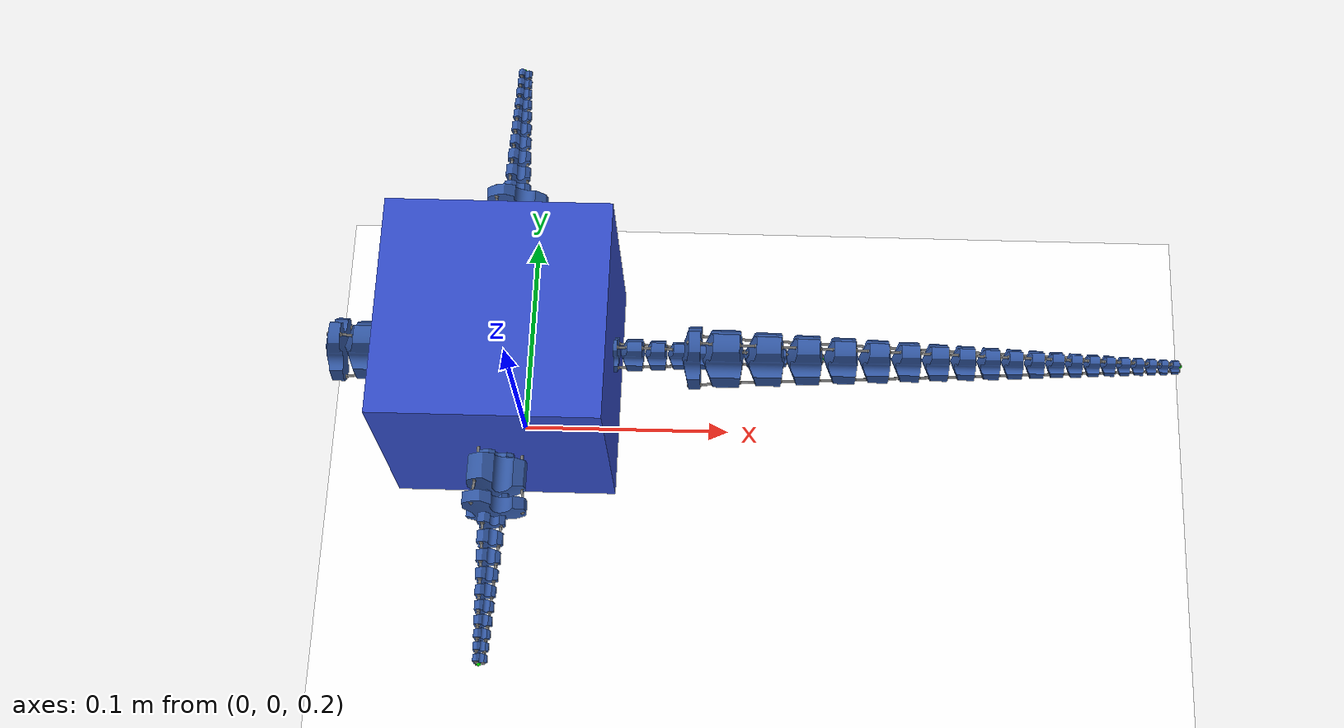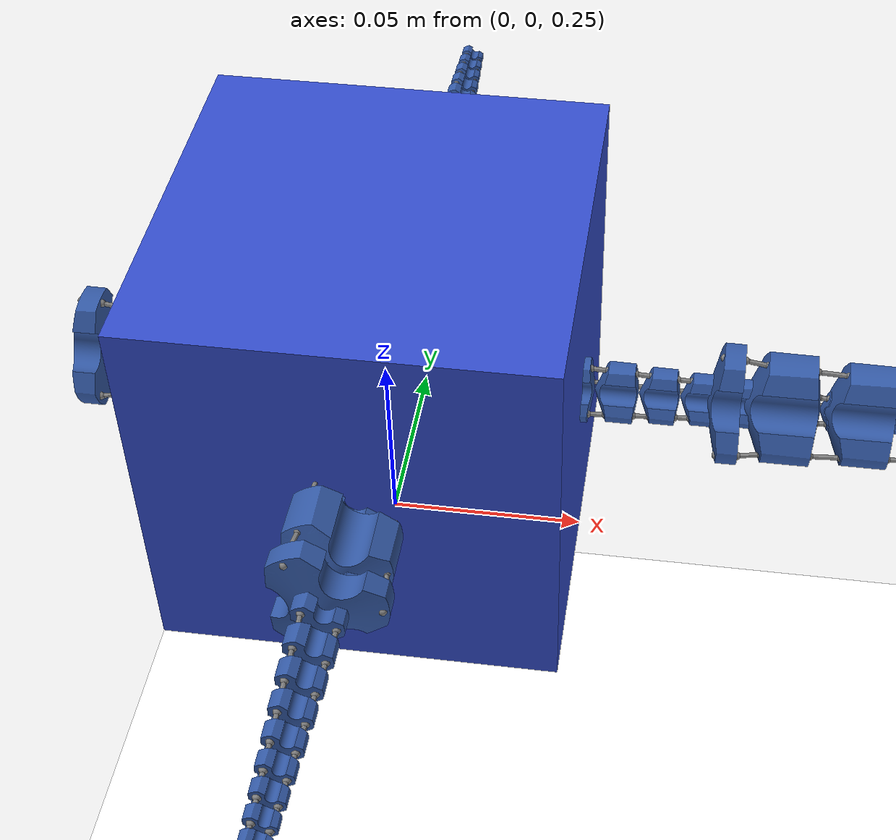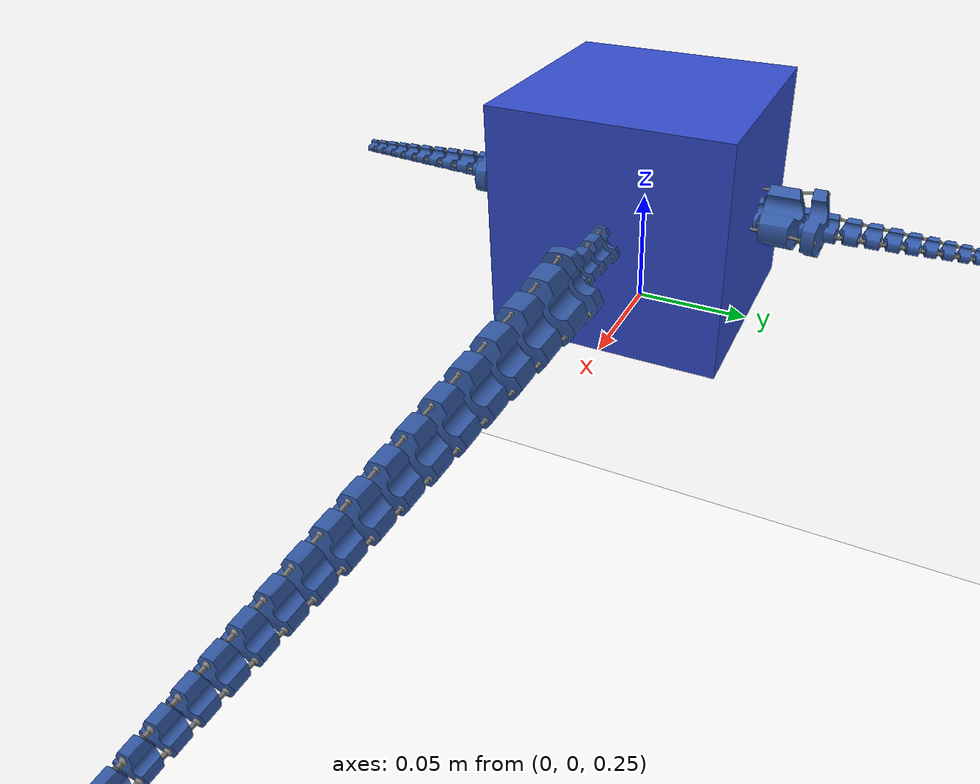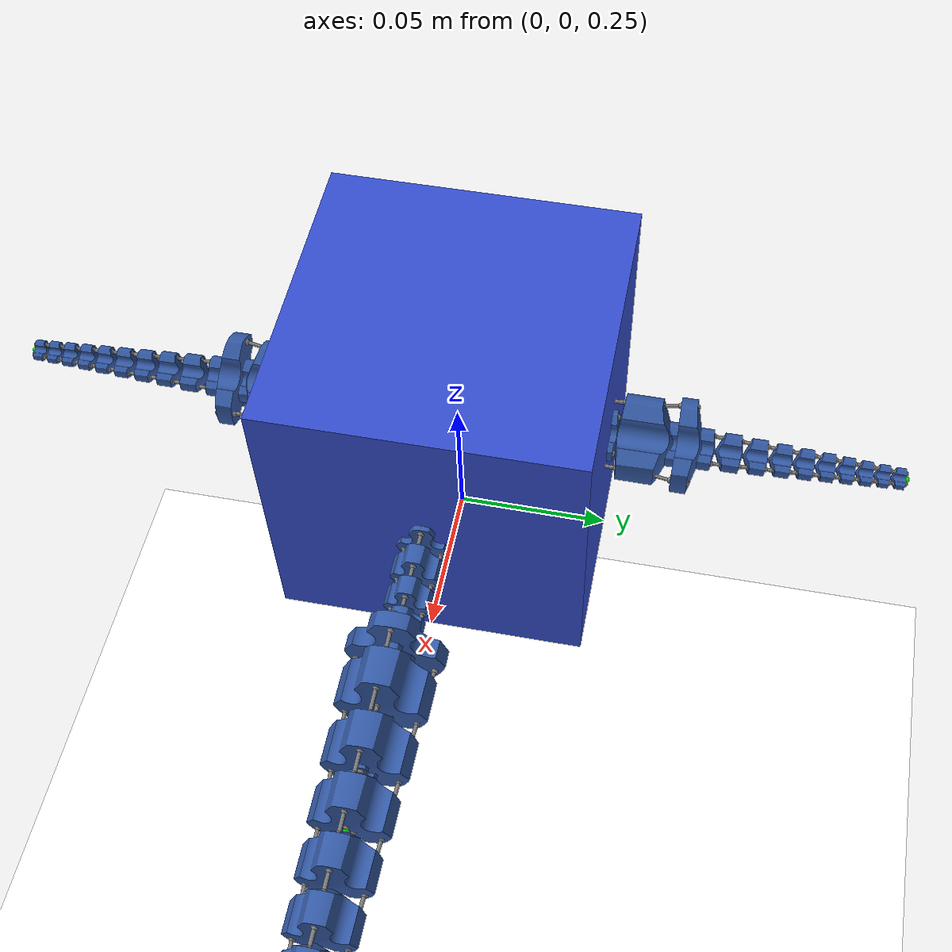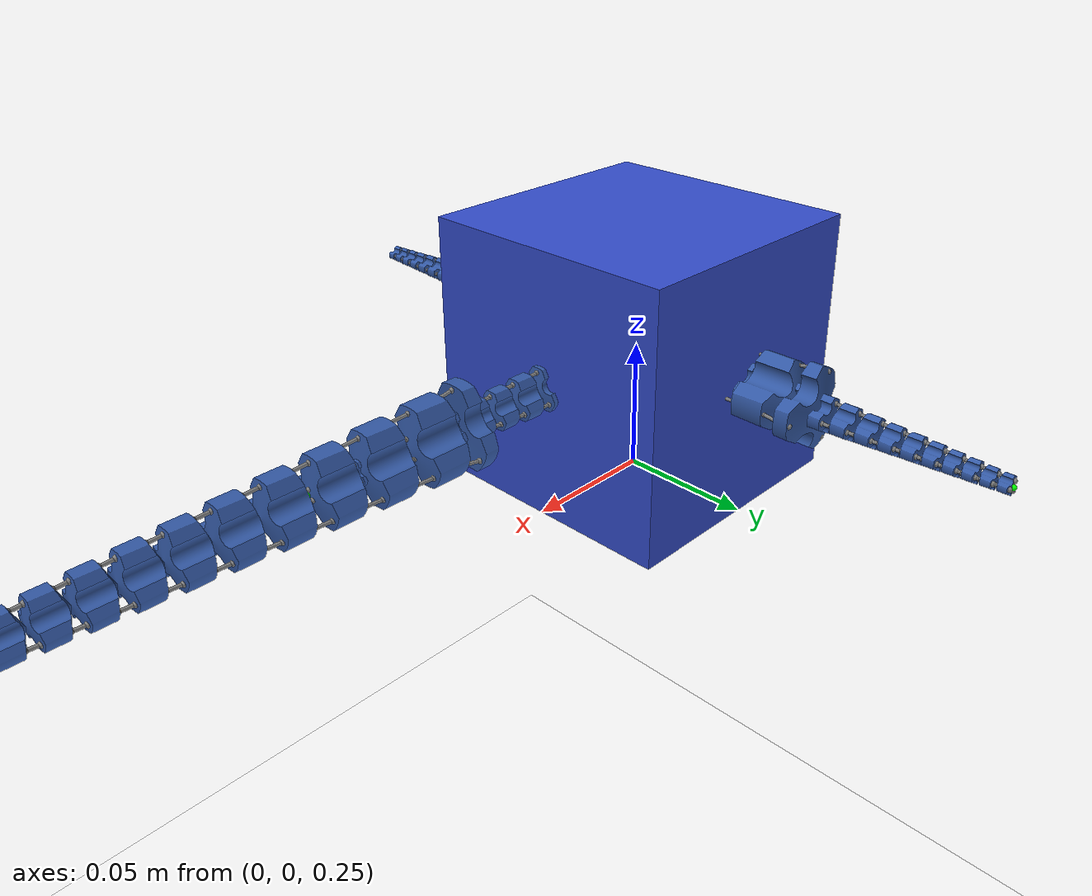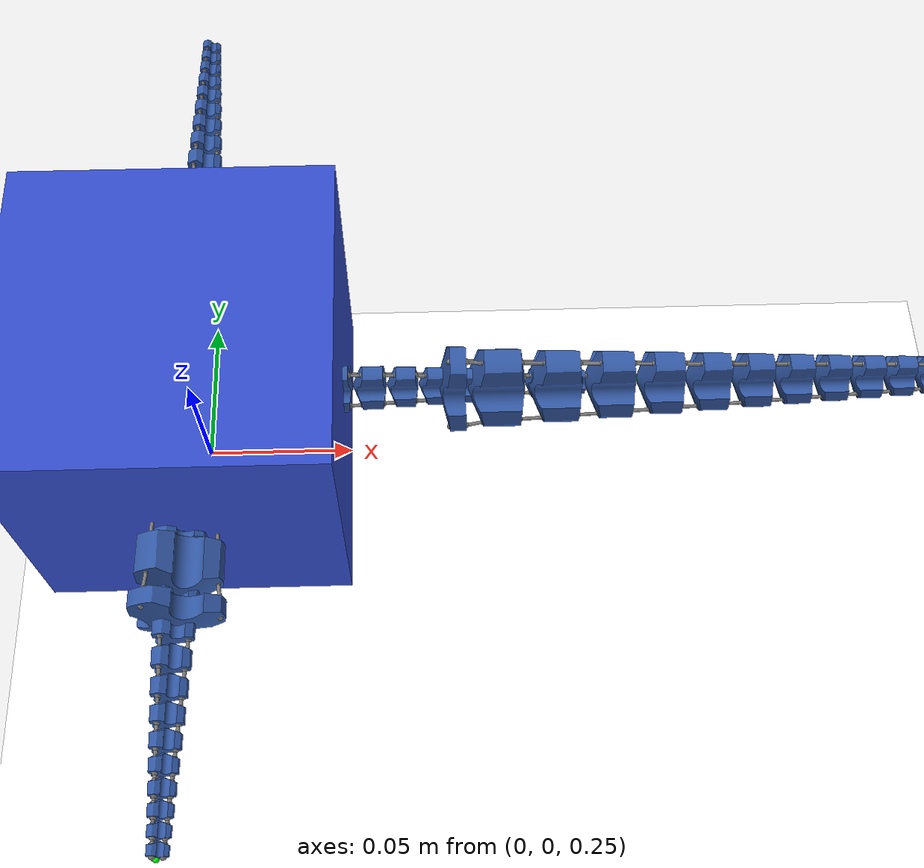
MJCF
<mujoco model="cube_with_spirob_arms">
  <compiler angle="radian" inertiafromgeom="true" autolimits="true" />
  <option timestep="0.002" gravity="0.0 0.0 -9.81" integrator="implicit" />
  <visual>
    <quality shadowsize="4096" />
    <map znear="0.01" zfar="20" />
    <scale connect="0" />
  </visual>
  <default>
    <geom density="1200.0" margin="0.001" rgba="0.2 0.35 0.65 1.0" friction="0.6 0.01 0.001" />
    <site size="0.001" />
    <joint damping="0.01" stiffness="0.2" limited="false" />
    <default class="cable_motor">
      <motor ctrllimited="true" ctrlrange="-10.0 0.0" gear="1.0" />
    </default>
  </default>
  <asset>
    <mesh name="link_001" file="meshes/link_001.stl" />
    <mesh name="link_002" file="meshes/link_002.stl" />
    <mesh name="link_003" file="meshes/link_003.stl" />
    <mesh name="link_004" file="meshes/link_004.stl" />
    <mesh name="link_005" file="meshes/link_005.stl" />
    <mesh name="link_006" file="meshes/link_006.stl" />
    <mesh name="link_007" file="meshes/link_007.stl" />
    <mesh name="link_008" file="meshes/link_008.stl" />
    <mesh name="link_009" file="meshes/link_009.stl" />
    <mesh name="link_010" file="meshes/link_010.stl" />
    <mesh name="link_011" file="meshes/link_011.stl" />
    <mesh name="link_012" file="meshes/link_012.stl" />
    <mesh name="link_013" file="meshes/link_013.stl" />
    <mesh name="link_014" file="meshes/link_014.stl" />
    <mesh name="link_015" file="meshes/link_015.stl" />
    <mesh name="link_016" file="meshes/link_016.stl" />
    <mesh name="link_017" file="meshes/link_017.stl" />
    <mesh name="link_018" file="meshes/link_018.stl" />
    <mesh name="link_019" file="meshes/link_019.stl" />
    <mesh name="link_020" file="meshes/link_020.stl" />
    <mesh name="link_021" file="meshes/link_021.stl" />
  </asset>
  <worldbody>
    <geom type="plane" size="2 2 0.05" rgba="1 1 1 1" />
    <body name="core" pos="0 0 0.3">
      <freejoint name="core_free" />
      <geom name="core_geom" type="box" size="0.05 0.05 0.05" rgba="0.2 0.3 0.8 1" />
      <body name="arm_px_mount" pos="0.08 0 0" quat="0.7071068 0.0 -0.7071068 0.0">
        <body name="px_link_001" pos="0 0 0" quat="0.0 0.0 -1.0 0.0">
          <joint name="px_j_001" type="ball" damping="50" stiffness="100" />
          <geom name="px_gmesh_001" type="mesh" mesh="link_001" group="1" />
          <site name="px_c0_001_s1" pos="-0.014043787134233146 0.0 0.003887071611887229" />
          <site name="px_c0_001_s2" pos="-0.013762963380968076 0.0 0.008989865749906125" />
          <site name="px_c1_001_s1" pos="0.007021893567116547 -0.01216227642358695 0.0038870716118872264" />
          <site name="px_c1_001_s2" pos="0.006881481690484012 -0.011919075919273306 0.008989865749906121" />
          <site name="px_c2_001_s1" pos="0.0070218935671165555 0.012162276423586946 0.0038870716118872264" />
          <site name="px_c2_001_s2" pos="0.006881481690484021 0.011919075919273303 0.008989865749906121" />
          <body name="px_link_002" pos="-6.469455238969971e-35 0.0 0.008584200393390806" quat="0.9999999999999989 0.0 1.656909611338257e-16 0.0">
            <joint name="px_j_002" type="ball" damping="0.009151416593531596" stiffness="0.18302833187063192" />
            <geom name="px_gmesh_002" type="mesh" mesh="link_002" group="1" />
            <site name="px_c0_002_s1" pos="-0.012813076370858354 0.0 0.0060753376579252534" />
            <site name="px_c0_002_s2" pos="-0.012165259019073867 0.0 0.017846701535654565" />
            <site name="px_c1_002_s1" pos="0.00640653818542915 -0.011096449637793441 0.006075337657925258" />
            <site name="px_c1_002_s2" pos="0.006082629509536907 -0.010535423354135714 0.01784670153565457" />
            <site name="px_c2_002_s1" pos="0.006406538185429157 0.011096449637793437 0.006075337657925258" />
            <site name="px_c2_002_s2" pos="0.006082629509536914 0.01053542335413571 0.01784670153565457" />
            <body name="px_link_003" pos="-1.2167588718591158e-34 0.0 0.019802434449997464" quat="0.9999999999999989 0.0 -1.3101234548921924e-16 0.0">
              <joint name="px_j_003" type="ball" damping="0.008374842566836545" stiffness="0.1674968513367309" />
              <geom name="px_gmesh_003" type="mesh" mesh="link_003" group="1" />
              <site name="px_c0_003_s1" pos="-0.011797748755937759 0.0 0.005644371041508834" />
              <site name="px_c0_003_s2" pos="-0.0111958856651136 0.0 0.016580708926176885" />
              <site name="px_c1_003_s1" pos="0.005898874377968848 -0.010217150130108339 0.005644371041508833" />
              <site name="px_c1_003_s2" pos="0.00559794283255677 -0.009695921403854396 0.016580708926176885" />
              <site name="px_c2_003_s1" pos="0.005898874377968856 0.010217150130108333 0.005644371041508833" />
              <site name="px_c2_003_s2" pos="0.005597942832556777 0.009695921403854392 0.016580708926176885" />
              <body name="px_link_004" pos="4.1249183207540277e-35 0.0 0.018397707889558357" quat="0.9999999999999989 0.0 -2.8387745732565563e-16 0.0">
                <joint name="px_j_004" type="ball" damping="0.007664167323436269" stiffness="0.15328334646872538" />
                <geom name="px_gmesh_004" type="mesh" mesh="link_004" group="1" />
                <site name="px_c0_004_s1" pos="-0.010854445501043577 0.0 0.0052439759315539925" />
                <site name="px_c0_004_s2" pos="-0.010295276810827758 0.0 0.015404522115493542" />
                <site name="px_c1_004_s1" pos="0.005427222750521765 -0.009400225547897434 0.005243975931553981" />
                <site name="px_c1_004_s2" pos="0.0051476384054138565 -0.008915971257169664 0.015404522115493532" />
                <site name="px_c2_004_s1" pos="0.005427222750521771 0.009400225547897429 0.005243975931553981" />
                <site name="px_c2_004_s2" pos="0.005147638405413862 0.008915971257169659 0.015404522115493532" />
                <body name="px_link_005" pos="1.190404145729528e-35 0.0 0.017092628507075464" quat="0.9999999999999989 0.0 3.3380155433229234e-16 0.0">
                  <joint name="px_j_005" type="ball" damping="0.00701379880192973" stiffness="0.1402759760385946" />
                  <geom name="px_gmesh_005" type="mesh" mesh="link_005" group="1" />
                  <site name="px_c0_005_s1" pos="-0.009978057409537241 0.0 0.004871983675149487" />
                  <site name="px_c0_005_s2" pos="-0.009458554504500285 0.0 0.01431177054390545" />
                  <site name="px_c1_005_s1" pos="0.004989028704768607 -0.008641251197078793 0.004871983675149488" />
                  <site name="px_c1_005_s2" pos="0.004729277252250129 -0.008191348483976972 0.01431177054390545" />
                  <site name="px_c2_005_s1" pos="0.004989028704768613 0.008641251197078788 0.004871983675149488" />
                  <site name="px_c2_005_s2" pos="0.0047292772522501345 0.008191348483976969 0.01431177054390545" />
                  <body name="px_link_006" pos="4.550835795716519e-35 0.0 0.01588012762430599" quat="0.9999999999999989 0.0 6.270311827459235e-20 0.0">
                    <joint name="px_j_006" type="ball" damping="0.006418619473967176" stiffness="0.1283723894793435" />
                    <geom name="px_gmesh_006" type="mesh" mesh="link_006" group="1" />
                    <site name="px_c0_006_s1" pos="-0.009163837716189213 0.0 0.004526379457254508" />
                    <site name="px_c0_006_s2" pos="-0.008681186821988264 0.0 0.01329653556051505" />
                    <site name="px_c1_006_s1" pos="0.004581918858094592 -0.007936116258377823 0.004526379457254509" />
                    <site name="px_c1_006_s2" pos="0.004340593410994118 -0.007518128322840526 0.01329653556051505" />
                    <site name="px_c2_006_s1" pos="0.004581918858094598 0.00793611625837782 0.004526379457254509" />
                    <site name="px_c2_006_s2" pos="0.0043405934109941235 0.007518128322840523 0.01329653556051505" />
                    <body name="px_link_007" pos="2.0482903766373542e-35 0.0 0.014753637994288443" quat="0.9999999999999989 0.0 -5.672128456715344e-17 0.0">
                      <joint name="px_j_007" type="ball" damping="0.005873946076162826" stiffness="0.11747892152325652" />
                      <geom name="px_gmesh_007" type="mesh" mesh="link_007" group="1" />
                      <site name="px_c0_007_s1" pos="-0.008407376377358998 0.0 0.004205291387891803" />
                      <site name="px_c0_007_s2" pos="-0.007958963320541919 0.0 0.012353318366142216" />
                      <site name="px_c1_007_s1" pos="0.004203688188679483 -0.0072810015219700675 0.004205291387891802" />
                      <site name="px_c1_007_s2" pos="0.003979481660270944 -0.006892664423377842 0.012353318366142216" />
                      <site name="px_c2_007_s1" pos="0.004203688188679488 0.007281001521970064 0.004205291387891802" />
                      <site name="px_c2_007_s2" pos="0.003979481660270949 0.006892664423377839 0.012353318366142216" />
                      <body name="px_link_008" pos="3.714119074183758e-36 0.0 0.013707058231279406" quat="0.9999999999999989 0.0 9.365505275997311e-17 0.0">
                        <joint name="px_j_008" type="ball" damping="0.005375492759090629" stiffness="0.10750985518181258" />
                        <geom name="px_gmesh_008" type="mesh" mesh="link_008" group="1" />
                        <site name="px_c0_008_s1" pos="-0.007704576184954142 0.0 0.003906980363463291" />
                        <site name="px_c0_008_s2" pos="-0.007287972233858338 0.0 0.011477010230276556" />
                        <site name="px_c1_008_s1" pos="0.0038522880924770557 -0.006672358701562873 0.0039069803634632925" />
                        <site name="px_c1_008_s2" pos="0.0036439861169291544 -0.0063115690965969366 0.011477010230276558" />
                        <site name="px_c2_008_s1" pos="0.003852288092477061 0.006672358701562869 0.0039069803634632925" />
                        <site name="px_c2_008_s2" pos="0.003643986116929159 0.006311569096596933 0.011477010230276558" />
                        <body name="px_link_009" pos="-1.3260761546955404e-36 0.0 0.012734719763926719" quat="0.9999999999999989 0.0 1.464790115601984e-17 0.0">
                          <joint name="px_j_009" type="ball" damping="0.004919337363395092" stiffness="0.09838674726790185" />
                          <geom name="px_gmesh_009" type="mesh" mesh="link_009" group="1" />
                          <site name="px_c0_009_s1" pos="-0.00705163057479501 0.0 0.0036298306472741363" />
                          <site name="px_c0_009_s2" pos="-0.0066645792848513425 0.0 0.010662864820750751" />
                          <site name="px_c1_009_s1" pos="0.0035258152873974885 -0.006106891215875532 0.003629830647274138" />
                          <site name="px_c1_009_s2" pos="0.003332289642425655 -0.005771694966216779 0.010662864820750753" />
                          <site name="px_c2_009_s1" pos="0.003525815287397493 0.00610689121587553 0.003629830647274138" />
                          <site name="px_c2_009_s2" pos="0.0033322896424256595 0.0057716949662167776 0.010662864820750753" />
                          <body name="px_link_010" pos="-2.4004641316690358e-35 0.0 0.011831356132687001" quat="0.9999999999999989 0.0 -2.0313861749255114e-16 0.0">
                            <joint name="px_j_010" type="ball" damping="0.004501890557655382" stiffness="0.09003781115310765" />
                            <geom name="px_gmesh_010" type="mesh" mesh="link_010" group="1" />
                            <site name="px_c0_010_s1" pos="-0.006445003009188863 0.0 0.003372341118246971" />
                            <site name="px_c0_010_s2" pos="-0.006085408001381059 0.0 0.009906472496266557" />
                            <site name="px_c1_010_s1" pos="0.003222501504594414 -0.005581536333424696 0.003372341118246968" />
                            <site name="px_c1_010_s2" pos="0.0030427040006905126 -0.005270117921589074 0.009906472496266553" />
                            <site name="px_c2_010_s1" pos="0.0032225015045944183 0.005581536333424694 0.003372341118246968" />
                            <site name="px_c2_010_s2" pos="0.003042704000690517 0.005270117921589072 0.009906472496266553" />
                            <body name="px_link_011" pos="2.1201211708008e-34 0.0 0.01099207446519479" quat="0.9999999999999989 0.0 1.3718854255569317e-16 0.0">
                              <joint name="px_j_011" type="ball" damping="0.004119867595159067" stiffness="0.08239735190318134" />
                              <geom name="px_gmesh_011" type="mesh" mesh="link_011" group="1" />
                              <site name="px_c0_011_s1" pos="-0.005881407822043716 0.0 0.003133117140426245" />
                              <site name="px_c0_011_s2" pos="-0.0055473214283280016 0.0 0.009203736422532638" />
                              <site name="px_c1_011_s1" pos="0.0029407039110218446 -0.005093448583906358 0.003133117140426245" />
                              <site name="px_c1_011_s2" pos="0.0027736607141639878 -0.0048041212798898185 0.009203736422532638" />
                              <site name="px_c2_011_s1" pos="0.0029407039110218476 0.005093448583906355 0.003133117140426245" />
                              <site name="px_c2_011_s2" pos="0.002773660714163991 0.004804121279889816 0.009203736422532638" />
                              <body name="px_link_012" pos="1.1996541848813755e-37 0.0 0.010212328975084867" quat="0.9999999999999989 0.0 1.5364155078561523e-17 0.0">
                                <joint name="px_j_012" type="ball" damping="0.0037702624673491797" stiffness="0.0754052493469836" />
                                <geom name="px_gmesh_012" type="mesh" mesh="link_012" group="1" />
                                <site name="px_c0_012_s1" pos="-0.005357792422773514 0.0 0.0029108630092366246" />
                                <site name="px_c0_012_s2" pos="-0.005047405136958841 0.0 0.008550850382654157" />
                                <site name="px_c1_012_s1" pos="0.0026788962113867432 -0.00463998434632563 0.002910863009236625" />
                                <site name="px_c1_012_s2" pos="0.002523702568479407 -0.004371181071798421 0.008550850382654157" />
                                <site name="px_c2_012_s1" pos="0.0026788962113867467 0.0046399843463256285 0.002910863009236625" />
                                <site name="px_c2_012_s2" pos="0.0025237025684794103 0.00437118107179842 0.008550850382654157" />
                                <body name="px_link_013" pos="-7.041604796568327e-36 0.0 0.009487896340730412" quat="0.9999999999999989 0.0 -7.460611667773275e-17 0.0">
                                  <joint name="px_j_013" type="ball" damping="0.0034503242505668657" stiffness="0.06900648501133731" />
                                  <geom name="px_gmesh_013" type="mesh" mesh="link_013" group="1" />
                                  <site name="px_c0_013_s1" pos="-0.004871320762606051 0.0 0.002704374933581111" />
                                  <site name="px_c0_013_s2" pos="-0.004582951439557895 0.0 0.007944278161587853" />
                                  <site name="px_c1_013_s1" pos="0.002435660381303012 -0.004218687530399415 0.0027043749335811103" />
                                  <site name="px_c1_013_s2" pos="0.0022914757197789342 -0.00396895237096759 0.007944278161587853" />
                                  <site name="px_c2_013_s1" pos="0.002435660381303015 0.004218687530399414 0.0027043749335811103" />
                                  <site name="px_c2_013_s2" pos="0.002291475719778937 0.0039689523709675895 0.007944278161587853" />
                                  <body name="px_link_014" pos="1.913567427110138e-35 0.0 0.008814852830541259" quat="0.9999999999999989 0.0 -3.0561124878616134e-17 0.0">
                                    <joint name="px_j_014" type="ball" damping="0.003157535459970208" stiffness="0.06315070919940417" />
                                    <geom name="px_gmesh_014" type="mesh" mesh="link_014" group="1" />
                                    <site name="px_c0_014_s1" pos="-0.0044193579737424465 0.0 0.0025125345157688836" />
                                    <site name="px_c0_014_s2" pos="-0.00415144472382633 0.0 0.007380734393003408" />
                                    <site name="px_c1_014_s1" pos="0.002209678986871211 -0.003827276273678272 0.0025125345157688823" />
                                    <site name="px_c1_014_s2" pos="0.002075722361913153 -0.003595256593240466 0.007380734393003407" />
                                    <site name="px_c2_014_s1" pos="0.0022096789868712133 0.003827276273678271 0.0025125345157688823" />
                                    <site name="px_c2_014_s2" pos="0.0020757223619131556 0.0035952565932404652 0.007380734393003407" />
                                    <body name="px_link_015" pos="6.361033776815479e-35 0.0 0.008189553050926335" quat="0.9999999999999989 0.0 3.460574972380459e-17 0.0">
                                      <joint name="px_j_015" type="ball" damping="0.002889592240303578" stiffness="0.057791844806071566" />
                                      <geom name="px_gmesh_015" type="mesh" mesh="link_015" group="1" />
                                      <site name="px_c0_015_s1" pos="-0.0039994560981695786 0.0 0.002334302693957652" />
                                      <site name="px_c0_015_s2" pos="-0.003750547827616025 0.0 0.006857166764812157" />
                                      <site name="px_c1_015_s1" pos="0.001999728049084778 -0.0034636305823354378 0.0023343026939576512" />
                                      <site name="px_c1_015_s2" pos="0.0018752739138080017 -0.00324806969682401 0.006857166764812156" />
                                      <site name="px_c2_015_s1" pos="0.0019997280490847806 0.0034636305823354356 0.0023343026939576512" />
                                      <site name="px_c2_015_s2" pos="0.001875273913808004 0.0032480696968240083 0.006857166764812156" />
                                      <body name="px_link_016" pos="3.5098889490189586e-35 0.0 0.007608610201813054" quat="0.9999999999999989 0.0 3.7669043585127384e-17 0.0">
                                        <joint name="px_j_016" type="ball" damping="0.0026443862376454305" stiffness="0.052887724752908614" />
                                        <geom name="px_gmesh_016" type="mesh" mesh="link_016" group="1" />
                                        <site name="px_c0_016_s1" pos="-0.003609340828828624 0.0 0.002168714114301612" />
                                        <site name="px_c0_016_s2" pos="-0.0033780893801997913 0.0 0.006370739486983523" />
                                        <site name="px_c1_016_s1" pos="0.001804670414414302 -0.0031257808486819623 0.002168714114301612" />
                                        <site name="px_c1_016_s2" pos="0.0016890446900998857 -0.0029255112195074404 0.006370739486983523" />
                                        <site name="px_c2_016_s1" pos="0.001804670414414304 0.003125780848681961 0.002168714114301612" />
                                        <site name="px_c2_016_s2" pos="0.0016890446900998878 0.0029255112195074396 0.006370739486983523" />
                                        <body name="px_link_017" pos="7.547270758475354e-36 0.0 0.0070688777327823915" quat="0.9999999999999989 0.0 -1.1446290600572686e-16 0.0">
                                          <joint name="px_j_017" type="ball" damping="0.002419988009489498" stiffness="0.048399760189789955" />
                                          <geom name="px_gmesh_017" type="mesh" mesh="link_017" group="1" />
                                          <site name="px_c0_017_s1" pos="-0.0032468991913262107 0.0 0.0020148719023225527" />
                                          <site name="px_c0_017_s2" pos="-0.0030320520415147373 0.0 0.005918817932105997" />
                                          <site name="px_c1_017_s1" pos="0.0016234495956630964 -0.002811897183215643 0.002014871902322551" />
                                          <site name="px_c1_017_s2" pos="0.00151602602075736 -0.0026258340935482257 0.0059188179321059955" />
                                          <site name="px_c2_017_s1" pos="0.0016234495956630984 0.0028118971832156417 0.002014871902322551" />
                                          <site name="px_c2_017_s2" pos="0.001516026020757362 0.002625834093548225 0.0059188179321059955" />
                                          <body name="px_link_018" pos="1.3493208599798276e-34 0.0 0.006567432300463999" quat="0.9999999999999989 0.0 9.93505334659414e-17 0.0">
                                            <joint name="px_j_018" type="ball" damping="0.002214631842618969" stiffness="0.04429263685237938" />
                                            <geom name="px_gmesh_018" type="mesh" mesh="link_018" group="1" />
                                            <site name="px_c0_018_s1" pos="-0.002910168099468794 0.0 0.0018719428051844347" />
                                            <site name="px_c0_018_s2" pos="-0.0027105615756791808 0.0 0.0054989543655012685" />
                                            <site name="px_c1_018_s1" pos="0.0014550840497343893 -0.0025202795034230487 0.0018719428051844345" />
                                            <site name="px_c1_018_s2" pos="0.0013552807878395828 -0.0023474151830601407 0.0054989543655012685" />
                                            <site name="px_c2_018_s1" pos="0.0014550840497343912 0.0025202795034230483 0.0018719428051844345" />
                                            <site name="px_c2_018_s2" pos="0.0013552807878395847 0.0023474151830601402 0.0054989543655012685" />
                                            <body name="px_link_019" pos="1.0404935640692325e-35 0.0 0.006101557934883262" quat="0.9999999999999989 0.0 -1.9838998241264484e-17 0.0">
                                              <joint name="px_j_019" type="ball" damping="0.0020267018593106683" stiffness="0.04053403718621337" />
                                              <geom name="px_gmesh_019" type="mesh" mesh="link_019" group="1" />
                                              <site name="px_c0_019_s1" pos="-0.0025973237226338207 0.0 0.0017391526785610904" />
                                              <site name="px_c0_019_s2" pos="-0.0024118766996021656 0.0 0.005108874687602738" />
                                              <site name="px_c1_019_s1" pos="0.0012986618613169034 -0.0022493483256528506 0.0017391526785610898" />
                                              <site name="px_c1_019_s2" pos="0.001205938349801076 -0.0020887464926512395 0.005108874687602738" />
                                              <site name="px_c2_019_s1" pos="0.001298661861316905 0.0022493483256528497 0.0017391526785610898" />
                                              <site name="px_c2_019_s2" pos="0.0012059383498010776 0.0020887464926512386 0.005108874687602738" />
                                              <body name="px_link_020" pos="-1.2294460807762836e-35 0.0 0.005668731329001503" quat="0.9999999999999989 0.0 1.502458610717566e-17 0.0">
                                                <joint name="px_j_020" type="ball" damping="0.0018547193025436988" stiffness="0.03709438605087398" />
                                                <geom name="px_gmesh_020" type="mesh" mesh="link_020" group="1" />
                                                <site name="px_c0_020_s1" pos="-0.0023066716073883893 0.0 0.0016157822936519741" />
                                                <site name="px_c0_020_s2" pos="-0.0021343796517028575 0.0 0.004746466116790304" />
                                                <site name="px_c1_020_s1" pos="0.0011533358036941884 -0.001997636210186625 0.001615782293651974" />
                                                <site name="px_c1_020_s2" pos="0.0010671898258514227 -0.001848426999695252 0.004746466116790304" />
                                                <site name="px_c2_020_s1" pos="0.0011533358036941899 0.0019976362101866243 0.001615782293651974" />
                                                <site name="px_c2_020_s2" pos="0.001067189825851424 0.001848426999695251 0.004746466116790304" />
                                                <body name="px_link_021" pos="7.551021878358898e-36 0.0 0.005266608171773102" quat="0.9999999999999989 0.0 -4.435904301331992e-16 0.0">
                                                  <joint name="px_j_021" type="ball" damping="0.0016973309001641753" stiffness="0.0339466180032835" />
                                                  <geom name="px_gmesh_021" type="mesh" mesh="link_021" group="1" />
                                                  <site name="px_c0_021_s1" pos="-0.0020366374998512533 0.0 0.0015011634416360086" />
                                                  <site name="px_c0_021_s2" pos="-0.0018765674296572542 0.0 0.004409765745968967" />
                                                  <site name="px_c1_021_s1" pos="0.0010183187499256225 -0.0017637798131712077 0.0015011634416360036" />
                                                  <site name="px_c1_021_s2" pos="0.0009382837148286231 -0.0016251550659976462 0.0044097657459689615" />
                                                  <site name="px_c2_021_s1" pos="0.0010183187499256236 0.001763779813171207 0.0015011634416360036" />
                                                  <site name="px_c2_021_s2" pos="0.0009382837148286242 0.0016251550659976456 0.0044097657459689615" />
                                                  <site name="px_tip_site" type="sphere" size="0.001" rgba="0 1 0 1" pos="0 0 0.005" />
                                                </body>
                                              </body>
                                            </body>
                                          </body>
                                        </body>
                                      </body>
                                    </body>
                                  </body>
                                </body>
                              </body>
                            </body>
                          </body>
                        </body>
                      </body>
                    </body>
                  </body>
                </body>
              </body>
            </body>
          </body>
        </body>
      </body>
      <body name="arm_nx_mount" pos="-0.08 0 0" quat="0.7071068 0.0000000 -0.7071068 0.0000000">
        <body name="nx_link_001" pos="0 0 0" quat="0.0 0.0 -1.0 0.0">
          <joint name="nx_j_001" type="ball" damping="50" stiffness="100" />
          <geom name="nx_gmesh_001" type="mesh" mesh="link_001" group="1" />
          <site name="nx_c0_001_s1" pos="-0.014043787134233146 0.0 0.003887071611887229" />
          <site name="nx_c0_001_s2" pos="-0.013762963380968076 0.0 0.008989865749906125" />
          <site name="nx_c1_001_s1" pos="0.007021893567116547 -0.01216227642358695 0.0038870716118872264" />
          <site name="nx_c1_001_s2" pos="0.006881481690484012 -0.011919075919273306 0.008989865749906121" />
          <site name="nx_c2_001_s1" pos="0.0070218935671165555 0.012162276423586946 0.0038870716118872264" />
          <site name="nx_c2_001_s2" pos="0.006881481690484021 0.011919075919273303 0.008989865749906121" />
          <body name="nx_link_002" pos="-6.469455238969971e-35 0.0 0.008584200393390806" quat="0.9999999999999989 0.0 1.656909611338257e-16 0.0">
            <joint name="nx_j_002" type="ball" damping="0.009151416593531596" stiffness="0.18302833187063192" />
            <geom name="nx_gmesh_002" type="mesh" mesh="link_002" group="1" />
            <site name="nx_c0_002_s1" pos="-0.012813076370858354 0.0 0.0060753376579252534" />
            <site name="nx_c0_002_s2" pos="-0.012165259019073867 0.0 0.017846701535654565" />
            <site name="nx_c1_002_s1" pos="0.00640653818542915 -0.011096449637793441 0.006075337657925258" />
            <site name="nx_c1_002_s2" pos="0.006082629509536907 -0.010535423354135714 0.01784670153565457" />
            <site name="nx_c2_002_s1" pos="0.006406538185429157 0.011096449637793437 0.006075337657925258" />
            <site name="nx_c2_002_s2" pos="0.006082629509536914 0.01053542335413571 0.01784670153565457" />
            <body name="nx_link_003" pos="-1.2167588718591158e-34 0.0 0.019802434449997464" quat="0.9999999999999989 0.0 -1.3101234548921924e-16 0.0">
              <joint name="nx_j_003" type="ball" damping="0.008374842566836545" stiffness="0.1674968513367309" />
              <geom name="nx_gmesh_003" type="mesh" mesh="link_003" group="1" />
              <site name="nx_c0_003_s1" pos="-0.011797748755937759 0.0 0.005644371041508834" />
              <site name="nx_c0_003_s2" pos="-0.0111958856651136 0.0 0.016580708926176885" />
              <site name="nx_c1_003_s1" pos="0.005898874377968848 -0.010217150130108339 0.005644371041508833" />
              <site name="nx_c1_003_s2" pos="0.00559794283255677 -0.009695921403854396 0.016580708926176885" />
              <site name="nx_c2_003_s1" pos="0.005898874377968856 0.010217150130108333 0.005644371041508833" />
              <site name="nx_c2_003_s2" pos="0.005597942832556777 0.009695921403854392 0.016580708926176885" />
              <body name="nx_link_004" pos="4.1249183207540277e-35 0.0 0.018397707889558357" quat="0.9999999999999989 0.0 -2.8387745732565563e-16 0.0">
                <joint name="nx_j_004" type="ball" damping="0.007664167323436269" stiffness="0.15328334646872538" />
                <geom name="nx_gmesh_004" type="mesh" mesh="link_004" group="1" />
                <site name="nx_c0_004_s1" pos="-0.010854445501043577 0.0 0.0052439759315539925" />
                <site name="nx_c0_004_s2" pos="-0.010295276810827758 0.0 0.015404522115493542" />
                <site name="nx_c1_004_s1" pos="0.005427222750521765 -0.009400225547897434 0.005243975931553981" />
                <site name="nx_c1_004_s2" pos="0.0051476384054138565 -0.008915971257169664 0.015404522115493532" />
                <site name="nx_c2_004_s1" pos="0.005427222750521771 0.009400225547897429 0.005243975931553981" />
                <site name="nx_c2_004_s2" pos="0.005147638405413862 0.008915971257169659 0.015404522115493532" />
                <body name="nx_link_005" pos="1.190404145729528e-35 0.0 0.017092628507075464" quat="0.9999999999999989 0.0 3.3380155433229234e-16 0.0">
                  <joint name="nx_j_005" type="ball" damping="0.00701379880192973" stiffness="0.1402759760385946" />
                  <geom name="nx_gmesh_005" type="mesh" mesh="link_005" group="1" />
                  <site name="nx_c0_005_s1" pos="-0.009978057409537241 0.0 0.004871983675149487" />
                  <site name="nx_c0_005_s2" pos="-0.009458554504500285 0.0 0.01431177054390545" />
                  <site name="nx_c1_005_s1" pos="0.004989028704768607 -0.008641251197078793 0.004871983675149488" />
                  <site name="nx_c1_005_s2" pos="0.004729277252250129 -0.008191348483976972 0.01431177054390545" />
                  <site name="nx_c2_005_s1" pos="0.004989028704768613 0.008641251197078788 0.004871983675149488" />
                  <site name="nx_c2_005_s2" pos="0.0047292772522501345 0.008191348483976969 0.01431177054390545" />
                  <body name="nx_link_006" pos="4.550835795716519e-35 0.0 0.01588012762430599" quat="0.9999999999999989 0.0 6.270311827459235e-20 0.0">
                    <joint name="nx_j_006" type="ball" damping="0.006418619473967176" stiffness="0.1283723894793435" />
                    <geom name="nx_gmesh_006" type="mesh" mesh="link_006" group="1" />
                    <site name="nx_c0_006_s1" pos="-0.009163837716189213 0.0 0.004526379457254508" />
                    <site name="nx_c0_006_s2" pos="-0.008681186821988264 0.0 0.01329653556051505" />
                    <site name="nx_c1_006_s1" pos="0.004581918858094592 -0.007936116258377823 0.004526379457254509" />
                    <site name="nx_c1_006_s2" pos="0.004340593410994118 -0.007518128322840526 0.01329653556051505" />
                    <site name="nx_c2_006_s1" pos="0.004581918858094598 0.00793611625837782 0.004526379457254509" />
                    <site name="nx_c2_006_s2" pos="0.0043405934109941235 0.007518128322840523 0.01329653556051505" />
                    <body name="nx_link_007" pos="2.0482903766373542e-35 0.0 0.014753637994288443" quat="0.9999999999999989 0.0 -5.672128456715344e-17 0.0">
                      <joint name="nx_j_007" type="ball" damping="0.005873946076162826" stiffness="0.11747892152325652" />
                      <geom name="nx_gmesh_007" type="mesh" mesh="link_007" group="1" />
                      <site name="nx_c0_007_s1" pos="-0.008407376377358998 0.0 0.004205291387891803" />
                      <site name="nx_c0_007_s2" pos="-0.007958963320541919 0.0 0.012353318366142216" />
                      <site name="nx_c1_007_s1" pos="0.004203688188679483 -0.0072810015219700675 0.004205291387891802" />
                      <site name="nx_c1_007_s2" pos="0.003979481660270944 -0.006892664423377842 0.012353318366142216" />
                      <site name="nx_c2_007_s1" pos="0.004203688188679488 0.007281001521970064 0.004205291387891802" />
                      <site name="nx_c2_007_s2" pos="0.003979481660270949 0.006892664423377839 0.012353318366142216" />
                      <body name="nx_link_008" pos="3.714119074183758e-36 0.0 0.013707058231279406" quat="0.9999999999999989 0.0 9.365505275997311e-17 0.0">
                        <joint name="nx_j_008" type="ball" damping="0.005375492759090629" stiffness="0.10750985518181258" />
                        <geom name="nx_gmesh_008" type="mesh" mesh="link_008" group="1" />
                        <site name="nx_c0_008_s1" pos="-0.007704576184954142 0.0 0.003906980363463291" />
                        <site name="nx_c0_008_s2" pos="-0.007287972233858338 0.0 0.011477010230276556" />
                        <site name="nx_c1_008_s1" pos="0.0038522880924770557 -0.006672358701562873 0.0039069803634632925" />
                        <site name="nx_c1_008_s2" pos="0.0036439861169291544 -0.0063115690965969366 0.011477010230276558" />
                        <site name="nx_c2_008_s1" pos="0.003852288092477061 0.006672358701562869 0.0039069803634632925" />
                        <site name="nx_c2_008_s2" pos="0.003643986116929159 0.006311569096596933 0.011477010230276558" />
                        <body name="nx_link_009" pos="-1.3260761546955404e-36 0.0 0.012734719763926719" quat="0.9999999999999989 0.0 1.464790115601984e-17 0.0">
                          <joint name="nx_j_009" type="ball" damping="0.004919337363395092" stiffness="0.09838674726790185" />
                          <geom name="nx_gmesh_009" type="mesh" mesh="link_009" group="1" />
                          <site name="nx_c0_009_s1" pos="-0.00705163057479501 0.0 0.0036298306472741363" />
                          <site name="nx_c0_009_s2" pos="-0.0066645792848513425 0.0 0.010662864820750751" />
                          <site name="nx_c1_009_s1" pos="0.0035258152873974885 -0.006106891215875532 0.003629830647274138" />
                          <site name="nx_c1_009_s2" pos="0.003332289642425655 -0.005771694966216779 0.010662864820750753" />
                          <site name="nx_c2_009_s1" pos="0.003525815287397493 0.00610689121587553 0.003629830647274138" />
                          <site name="nx_c2_009_s2" pos="0.0033322896424256595 0.0057716949662167776 0.010662864820750753" />
                          <body name="nx_link_010" pos="-2.4004641316690358e-35 0.0 0.011831356132687001" quat="0.9999999999999989 0.0 -2.0313861749255114e-16 0.0">
                            <joint name="nx_j_010" type="ball" damping="0.004501890557655382" stiffness="0.09003781115310765" />
                            <geom name="nx_gmesh_010" type="mesh" mesh="link_010" group="1" />
                            <site name="nx_c0_010_s1" pos="-0.006445003009188863 0.0 0.003372341118246971" />
                            <site name="nx_c0_010_s2" pos="-0.006085408001381059 0.0 0.009906472496266557" />
                            <site name="nx_c1_010_s1" pos="0.003222501504594414 -0.005581536333424696 0.003372341118246968" />
                            <site name="nx_c1_010_s2" pos="0.0030427040006905126 -0.005270117921589074 0.009906472496266553" />
                            <site name="nx_c2_010_s1" pos="0.0032225015045944183 0.005581536333424694 0.003372341118246968" />
                            <site name="nx_c2_010_s2" pos="0.003042704000690517 0.005270117921589072 0.009906472496266553" />
                            <body name="nx_link_011" pos="2.1201211708008e-34 0.0 0.01099207446519479" quat="0.9999999999999989 0.0 1.3718854255569317e-16 0.0">
                              <joint name="nx_j_011" type="ball" damping="0.004119867595159067" stiffness="0.08239735190318134" />
                              <geom name="nx_gmesh_011" type="mesh" mesh="link_011" group="1" />
                              <site name="nx_c0_011_s1" pos="-0.005881407822043716 0.0 0.003133117140426245" />
                              <site name="nx_c0_011_s2" pos="-0.0055473214283280016 0.0 0.009203736422532638" />
                              <site name="nx_c1_011_s1" pos="0.0029407039110218446 -0.005093448583906358 0.003133117140426245" />
                              <site name="nx_c1_011_s2" pos="0.0027736607141639878 -0.0048041212798898185 0.009203736422532638" />
                              <site name="nx_c2_011_s1" pos="0.0029407039110218476 0.005093448583906355 0.003133117140426245" />
                              <site name="nx_c2_011_s2" pos="0.002773660714163991 0.004804121279889816 0.009203736422532638" />
                              <body name="nx_link_012" pos="1.1996541848813755e-37 0.0 0.010212328975084867" quat="0.9999999999999989 0.0 1.5364155078561523e-17 0.0">
                                <joint name="nx_j_012" type="ball" damping="0.0037702624673491797" stiffness="0.0754052493469836" />
                                <geom name="nx_gmesh_012" type="mesh" mesh="link_012" group="1" />
                                <site name="nx_c0_012_s1" pos="-0.005357792422773514 0.0 0.0029108630092366246" />
                                <site name="nx_c0_012_s2" pos="-0.005047405136958841 0.0 0.008550850382654157" />
                                <site name="nx_c1_012_s1" pos="0.0026788962113867432 -0.00463998434632563 0.002910863009236625" />
                                <site name="nx_c1_012_s2" pos="0.002523702568479407 -0.004371181071798421 0.008550850382654157" />
                                <site name="nx_c2_012_s1" pos="0.0026788962113867467 0.0046399843463256285 0.002910863009236625" />
                                <site name="nx_c2_012_s2" pos="0.0025237025684794103 0.00437118107179842 0.008550850382654157" />
                                <body name="nx_link_013" pos="-7.041604796568327e-36 0.0 0.009487896340730412" quat="0.9999999999999989 0.0 -7.460611667773275e-17 0.0">
                                  <joint name="nx_j_013" type="ball" damping="0.0034503242505668657" stiffness="0.06900648501133731" />
                                  <geom name="nx_gmesh_013" type="mesh" mesh="link_013" group="1" />
                                  <site name="nx_c0_013_s1" pos="-0.004871320762606051 0.0 0.002704374933581111" />
                                  <site name="nx_c0_013_s2" pos="-0.004582951439557895 0.0 0.007944278161587853" />
                                  <site name="nx_c1_013_s1" pos="0.002435660381303012 -0.004218687530399415 0.0027043749335811103" />
                                  <site name="nx_c1_013_s2" pos="0.0022914757197789342 -0.00396895237096759 0.007944278161587853" />
                                  <site name="nx_c2_013_s1" pos="0.002435660381303015 0.004218687530399414 0.0027043749335811103" />
                                  <site name="nx_c2_013_s2" pos="0.002291475719778937 0.0039689523709675895 0.007944278161587853" />
                                  <body name="nx_link_014" pos="1.913567427110138e-35 0.0 0.008814852830541259" quat="0.9999999999999989 0.0 -3.0561124878616134e-17 0.0">
                                    <joint name="nx_j_014" type="ball" damping="0.003157535459970208" stiffness="0.06315070919940417" />
                                    <geom name="nx_gmesh_014" type="mesh" mesh="link_014" group="1" />
                                    <site name="nx_c0_014_s1" pos="-0.0044193579737424465 0.0 0.0025125345157688836" />
                                    <site name="nx_c0_014_s2" pos="-0.00415144472382633 0.0 0.007380734393003408" />
                                    <site name="nx_c1_014_s1" pos="0.002209678986871211 -0.003827276273678272 0.0025125345157688823" />
                                    <site name="nx_c1_014_s2" pos="0.002075722361913153 -0.003595256593240466 0.007380734393003407" />
                                    <site name="nx_c2_014_s1" pos="0.0022096789868712133 0.003827276273678271 0.0025125345157688823" />
                                    <site name="nx_c2_014_s2" pos="0.0020757223619131556 0.0035952565932404652 0.007380734393003407" />
                                    <body name="nx_link_015" pos="6.361033776815479e-35 0.0 0.008189553050926335" quat="0.9999999999999989 0.0 3.460574972380459e-17 0.0">
                                      <joint name="nx_j_015" type="ball" damping="0.002889592240303578" stiffness="0.057791844806071566" />
                                      <geom name="nx_gmesh_015" type="mesh" mesh="link_015" group="1" />
                                      <site name="nx_c0_015_s1" pos="-0.0039994560981695786 0.0 0.002334302693957652" />
                                      <site name="nx_c0_015_s2" pos="-0.003750547827616025 0.0 0.006857166764812157" />
                                      <site name="nx_c1_015_s1" pos="0.001999728049084778 -0.0034636305823354378 0.0023343026939576512" />
                                      <site name="nx_c1_015_s2" pos="0.0018752739138080017 -0.00324806969682401 0.006857166764812156" />
                                      <site name="nx_c2_015_s1" pos="0.0019997280490847806 0.0034636305823354356 0.0023343026939576512" />
                                      <site name="nx_c2_015_s2" pos="0.001875273913808004 0.0032480696968240083 0.006857166764812156" />
                                      <body name="nx_link_016" pos="3.5098889490189586e-35 0.0 0.007608610201813054" quat="0.9999999999999989 0.0 3.7669043585127384e-17 0.0">
                                        <joint name="nx_j_016" type="ball" damping="0.0026443862376454305" stiffness="0.052887724752908614" />
                                        <geom name="nx_gmesh_016" type="mesh" mesh="link_016" group="1" />
                                        <site name="nx_c0_016_s1" pos="-0.003609340828828624 0.0 0.002168714114301612" />
                                        <site name="nx_c0_016_s2" pos="-0.0033780893801997913 0.0 0.006370739486983523" />
                                        <site name="nx_c1_016_s1" pos="0.001804670414414302 -0.0031257808486819623 0.002168714114301612" />
                                        <site name="nx_c1_016_s2" pos="0.0016890446900998857 -0.0029255112195074404 0.006370739486983523" />
                                        <site name="nx_c2_016_s1" pos="0.001804670414414304 0.003125780848681961 0.002168714114301612" />
                                        <site name="nx_c2_016_s2" pos="0.0016890446900998878 0.0029255112195074396 0.006370739486983523" />
                                        <body name="nx_link_017" pos="7.547270758475354e-36 0.0 0.0070688777327823915" quat="0.9999999999999989 0.0 -1.1446290600572686e-16 0.0">
                                          <joint name="nx_j_017" type="ball" damping="0.002419988009489498" stiffness="0.048399760189789955" />
                                          <geom name="nx_gmesh_017" type="mesh" mesh="link_017" group="1" />
                                          <site name="nx_c0_017_s1" pos="-0.0032468991913262107 0.0 0.0020148719023225527" />
                                          <site name="nx_c0_017_s2" pos="-0.0030320520415147373 0.0 0.005918817932105997" />
                                          <site name="nx_c1_017_s1" pos="0.0016234495956630964 -0.002811897183215643 0.002014871902322551" />
                                          <site name="nx_c1_017_s2" pos="0.00151602602075736 -0.0026258340935482257 0.0059188179321059955" />
                                          <site name="nx_c2_017_s1" pos="0.0016234495956630984 0.0028118971832156417 0.002014871902322551" />
                                          <site name="nx_c2_017_s2" pos="0.001516026020757362 0.002625834093548225 0.0059188179321059955" />
                                          <body name="nx_link_018" pos="1.3493208599798276e-34 0.0 0.006567432300463999" quat="0.9999999999999989 0.0 9.93505334659414e-17 0.0">
                                            <joint name="nx_j_018" type="ball" damping="0.002214631842618969" stiffness="0.04429263685237938" />
                                            <geom name="nx_gmesh_018" type="mesh" mesh="link_018" group="1" />
                                            <site name="nx_c0_018_s1" pos="-0.002910168099468794 0.0 0.0018719428051844347" />
                                            <site name="nx_c0_018_s2" pos="-0.0027105615756791808 0.0 0.0054989543655012685" />
                                            <site name="nx_c1_018_s1" pos="0.0014550840497343893 -0.0025202795034230487 0.0018719428051844345" />
                                            <site name="nx_c1_018_s2" pos="0.0013552807878395828 -0.0023474151830601407 0.0054989543655012685" />
                                            <site name="nx_c2_018_s1" pos="0.0014550840497343912 0.0025202795034230483 0.0018719428051844345" />
                                            <site name="nx_c2_018_s2" pos="0.0013552807878395847 0.0023474151830601402 0.0054989543655012685" />
                                            <body name="nx_link_019" pos="1.0404935640692325e-35 0.0 0.006101557934883262" quat="0.9999999999999989 0.0 -1.9838998241264484e-17 0.0">
                                              <joint name="nx_j_019" type="ball" damping="0.0020267018593106683" stiffness="0.04053403718621337" />
                                              <geom name="nx_gmesh_019" type="mesh" mesh="link_019" group="1" />
                                              <site name="nx_c0_019_s1" pos="-0.0025973237226338207 0.0 0.0017391526785610904" />
                                              <site name="nx_c0_019_s2" pos="-0.0024118766996021656 0.0 0.005108874687602738" />
                                              <site name="nx_c1_019_s1" pos="0.0012986618613169034 -0.0022493483256528506 0.0017391526785610898" />
                                              <site name="nx_c1_019_s2" pos="0.001205938349801076 -0.0020887464926512395 0.005108874687602738" />
                                              <site name="nx_c2_019_s1" pos="0.001298661861316905 0.0022493483256528497 0.0017391526785610898" />
                                              <site name="nx_c2_019_s2" pos="0.0012059383498010776 0.0020887464926512386 0.005108874687602738" />
                                              <body name="nx_link_020" pos="-1.2294460807762836e-35 0.0 0.005668731329001503" quat="0.9999999999999989 0.0 1.502458610717566e-17 0.0">
                                                <joint name="nx_j_020" type="ball" damping="0.0018547193025436988" stiffness="0.03709438605087398" />
                                                <geom name="nx_gmesh_020" type="mesh" mesh="link_020" group="1" />
                                                <site name="nx_c0_020_s1" pos="-0.0023066716073883893 0.0 0.0016157822936519741" />
                                                <site name="nx_c0_020_s2" pos="-0.0021343796517028575 0.0 0.004746466116790304" />
                                                <site name="nx_c1_020_s1" pos="0.0011533358036941884 -0.001997636210186625 0.001615782293651974" />
                                                <site name="nx_c1_020_s2" pos="0.0010671898258514227 -0.001848426999695252 0.004746466116790304" />
                                                <site name="nx_c2_020_s1" pos="0.0011533358036941899 0.0019976362101866243 0.001615782293651974" />
                                                <site name="nx_c2_020_s2" pos="0.001067189825851424 0.001848426999695251 0.004746466116790304" />
                                                <body name="nx_link_021" pos="7.551021878358898e-36 0.0 0.005266608171773102" quat="0.9999999999999989 0.0 -4.435904301331992e-16 0.0">
                                                  <joint name="nx_j_021" type="ball" damping="0.0016973309001641753" stiffness="0.0339466180032835" />
                                                  <geom name="nx_gmesh_021" type="mesh" mesh="link_021" group="1" />
                                                  <site name="nx_c0_021_s1" pos="-0.0020366374998512533 0.0 0.0015011634416360086" />
                                                  <site name="nx_c0_021_s2" pos="-0.0018765674296572542 0.0 0.004409765745968967" />
                                                  <site name="nx_c1_021_s1" pos="0.0010183187499256225 -0.0017637798131712077 0.0015011634416360036" />
                                                  <site name="nx_c1_021_s2" pos="0.0009382837148286231 -0.0016251550659976462 0.0044097657459689615" />
                                                  <site name="nx_c2_021_s1" pos="0.0010183187499256236 0.001763779813171207 0.0015011634416360036" />
                                                  <site name="nx_c2_021_s2" pos="0.0009382837148286242 0.0016251550659976456 0.0044097657459689615" />
                                                  <site name="nx_tip_site" type="sphere" size="0.001" rgba="0 1 0 1" pos="0 0 0.005" />
                                                </body>
                                              </body>
                                            </body>
                                          </body>
                                        </body>
                                      </body>
                                    </body>
                                  </body>
                                </body>
                              </body>
                            </body>
                          </body>
                        </body>
                      </body>
                    </body>
                  </body>
                </body>
              </body>
            </body>
          </body>
        </body>
      </body>
      <body name="arm_py_mount" pos="0 0.08 0" quat="0.7071068 -0.7071068 0.0000000 0.0000000">
        <body name="py_link_001" pos="0 0 0" quat="0.0 0.0 -1.0 0.0">
          <joint name="py_j_001" type="ball" damping="50" stiffness="100" />
          <geom name="py_gmesh_001" type="mesh" mesh="link_001" group="1" />
          <site name="py_c0_001_s1" pos="-0.014043787134233146 0.0 0.003887071611887229" />
          <site name="py_c0_001_s2" pos="-0.013762963380968076 0.0 0.008989865749906125" />
          <site name="py_c1_001_s1" pos="0.007021893567116547 -0.01216227642358695 0.0038870716118872264" />
          <site name="py_c1_001_s2" pos="0.006881481690484012 -0.011919075919273306 0.008989865749906121" />
          <site name="py_c2_001_s1" pos="0.0070218935671165555 0.012162276423586946 0.0038870716118872264" />
          <site name="py_c2_001_s2" pos="0.006881481690484021 0.011919075919273303 0.008989865749906121" />
          <body name="py_link_002" pos="-6.469455238969971e-35 0.0 0.008584200393390806" quat="0.9999999999999989 0.0 1.656909611338257e-16 0.0">
            <joint name="py_j_002" type="ball" damping="0.009151416593531596" stiffness="0.18302833187063192" />
            <geom name="py_gmesh_002" type="mesh" mesh="link_002" group="1" />
            <site name="py_c0_002_s1" pos="-0.012813076370858354 0.0 0.0060753376579252534" />
            <site name="py_c0_002_s2" pos="-0.012165259019073867 0.0 0.017846701535654565" />
            <site name="py_c1_002_s1" pos="0.00640653818542915 -0.011096449637793441 0.006075337657925258" />
            <site name="py_c1_002_s2" pos="0.006082629509536907 -0.010535423354135714 0.01784670153565457" />
            <site name="py_c2_002_s1" pos="0.006406538185429157 0.011096449637793437 0.006075337657925258" />
            <site name="py_c2_002_s2" pos="0.006082629509536914 0.01053542335413571 0.01784670153565457" />
            <body name="py_link_003" pos="-1.2167588718591158e-34 0.0 0.019802434449997464" quat="0.9999999999999989 0.0 -1.3101234548921924e-16 0.0">
              <joint name="py_j_003" type="ball" damping="0.008374842566836545" stiffness="0.1674968513367309" />
              <geom name="py_gmesh_003" type="mesh" mesh="link_003" group="1" />
              <site name="py_c0_003_s1" pos="-0.011797748755937759 0.0 0.005644371041508834" />
              <site name="py_c0_003_s2" pos="-0.0111958856651136 0.0 0.016580708926176885" />
              <site name="py_c1_003_s1" pos="0.005898874377968848 -0.010217150130108339 0.005644371041508833" />
              <site name="py_c1_003_s2" pos="0.00559794283255677 -0.009695921403854396 0.016580708926176885" />
              <site name="py_c2_003_s1" pos="0.005898874377968856 0.010217150130108333 0.005644371041508833" />
              <site name="py_c2_003_s2" pos="0.005597942832556777 0.009695921403854392 0.016580708926176885" />
              <body name="py_link_004" pos="4.1249183207540277e-35 0.0 0.018397707889558357" quat="0.9999999999999989 0.0 -2.8387745732565563e-16 0.0">
                <joint name="py_j_004" type="ball" damping="0.007664167323436269" stiffness="0.15328334646872538" />
                <geom name="py_gmesh_004" type="mesh" mesh="link_004" group="1" />
                <site name="py_c0_004_s1" pos="-0.010854445501043577 0.0 0.0052439759315539925" />
                <site name="py_c0_004_s2" pos="-0.010295276810827758 0.0 0.015404522115493542" />
                <site name="py_c1_004_s1" pos="0.005427222750521765 -0.009400225547897434 0.005243975931553981" />
                <site name="py_c1_004_s2" pos="0.0051476384054138565 -0.008915971257169664 0.015404522115493532" />
                <site name="py_c2_004_s1" pos="0.005427222750521771 0.009400225547897429 0.005243975931553981" />
                <site name="py_c2_004_s2" pos="0.005147638405413862 0.008915971257169659 0.015404522115493532" />
                <body name="py_link_005" pos="1.190404145729528e-35 0.0 0.017092628507075464" quat="0.9999999999999989 0.0 3.3380155433229234e-16 0.0">
                  <joint name="py_j_005" type="ball" damping="0.00701379880192973" stiffness="0.1402759760385946" />
                  <geom name="py_gmesh_005" type="mesh" mesh="link_005" group="1" />
                  <site name="py_c0_005_s1" pos="-0.009978057409537241 0.0 0.004871983675149487" />
                  <site name="py_c0_005_s2" pos="-0.009458554504500285 0.0 0.01431177054390545" />
                  <site name="py_c1_005_s1" pos="0.004989028704768607 -0.008641251197078793 0.004871983675149488" />
                  <site name="py_c1_005_s2" pos="0.004729277252250129 -0.008191348483976972 0.01431177054390545" />
                  <site name="py_c2_005_s1" pos="0.004989028704768613 0.008641251197078788 0.004871983675149488" />
                  <site name="py_c2_005_s2" pos="0.0047292772522501345 0.008191348483976969 0.01431177054390545" />
                  <body name="py_link_006" pos="4.550835795716519e-35 0.0 0.01588012762430599" quat="0.9999999999999989 0.0 6.270311827459235e-20 0.0">
                    <joint name="py_j_006" type="ball" damping="0.006418619473967176" stiffness="0.1283723894793435" />
                    <geom name="py_gmesh_006" type="mesh" mesh="link_006" group="1" />
                    <site name="py_c0_006_s1" pos="-0.009163837716189213 0.0 0.004526379457254508" />
                    <site name="py_c0_006_s2" pos="-0.008681186821988264 0.0 0.01329653556051505" />
                    <site name="py_c1_006_s1" pos="0.004581918858094592 -0.007936116258377823 0.004526379457254509" />
                    <site name="py_c1_006_s2" pos="0.004340593410994118 -0.007518128322840526 0.01329653556051505" />
                    <site name="py_c2_006_s1" pos="0.004581918858094598 0.00793611625837782 0.004526379457254509" />
                    <site name="py_c2_006_s2" pos="0.0043405934109941235 0.007518128322840523 0.01329653556051505" />
                    <body name="py_link_007" pos="2.0482903766373542e-35 0.0 0.014753637994288443" quat="0.9999999999999989 0.0 -5.672128456715344e-17 0.0">
                      <joint name="py_j_007" type="ball" damping="0.005873946076162826" stiffness="0.11747892152325652" />
                      <geom name="py_gmesh_007" type="mesh" mesh="link_007" group="1" />
                      <site name="py_c0_007_s1" pos="-0.008407376377358998 0.0 0.004205291387891803" />
                      <site name="py_c0_007_s2" pos="-0.007958963320541919 0.0 0.012353318366142216" />
                      <site name="py_c1_007_s1" pos="0.004203688188679483 -0.0072810015219700675 0.004205291387891802" />
                      <site name="py_c1_007_s2" pos="0.003979481660270944 -0.006892664423377842 0.012353318366142216" />
                      <site name="py_c2_007_s1" pos="0.004203688188679488 0.007281001521970064 0.004205291387891802" />
                      <site name="py_c2_007_s2" pos="0.003979481660270949 0.006892664423377839 0.012353318366142216" />
                      <body name="py_link_008" pos="3.714119074183758e-36 0.0 0.013707058231279406" quat="0.9999999999999989 0.0 9.365505275997311e-17 0.0">
                        <joint name="py_j_008" type="ball" damping="0.005375492759090629" stiffness="0.10750985518181258" />
                        <geom name="py_gmesh_008" type="mesh" mesh="link_008" group="1" />
                        <site name="py_c0_008_s1" pos="-0.007704576184954142 0.0 0.003906980363463291" />
                        <site name="py_c0_008_s2" pos="-0.007287972233858338 0.0 0.011477010230276556" />
                        <site name="py_c1_008_s1" pos="0.0038522880924770557 -0.006672358701562873 0.0039069803634632925" />
                        <site name="py_c1_008_s2" pos="0.0036439861169291544 -0.0063115690965969366 0.011477010230276558" />
                        <site name="py_c2_008_s1" pos="0.003852288092477061 0.006672358701562869 0.0039069803634632925" />
                        <site name="py_c2_008_s2" pos="0.003643986116929159 0.006311569096596933 0.011477010230276558" />
                        <body name="py_link_009" pos="-1.3260761546955404e-36 0.0 0.012734719763926719" quat="0.9999999999999989 0.0 1.464790115601984e-17 0.0">
                          <joint name="py_j_009" type="ball" damping="0.004919337363395092" stiffness="0.09838674726790185" />
                          <geom name="py_gmesh_009" type="mesh" mesh="link_009" group="1" />
                          <site name="py_c0_009_s1" pos="-0.00705163057479501 0.0 0.0036298306472741363" />
                          <site name="py_c0_009_s2" pos="-0.0066645792848513425 0.0 0.010662864820750751" />
                          <site name="py_c1_009_s1" pos="0.0035258152873974885 -0.006106891215875532 0.003629830647274138" />
                          <site name="py_c1_009_s2" pos="0.003332289642425655 -0.005771694966216779 0.010662864820750753" />
                          <site name="py_c2_009_s1" pos="0.003525815287397493 0.00610689121587553 0.003629830647274138" />
                          <site name="py_c2_009_s2" pos="0.0033322896424256595 0.0057716949662167776 0.010662864820750753" />
                          <body name="py_link_010" pos="-2.4004641316690358e-35 0.0 0.011831356132687001" quat="0.9999999999999989 0.0 -2.0313861749255114e-16 0.0">
                            <joint name="py_j_010" type="ball" damping="0.004501890557655382" stiffness="0.09003781115310765" />
                            <geom name="py_gmesh_010" type="mesh" mesh="link_010" group="1" />
                            <site name="py_c0_010_s1" pos="-0.006445003009188863 0.0 0.003372341118246971" />
                            <site name="py_c0_010_s2" pos="-0.006085408001381059 0.0 0.009906472496266557" />
                            <site name="py_c1_010_s1" pos="0.003222501504594414 -0.005581536333424696 0.003372341118246968" />
                            <site name="py_c1_010_s2" pos="0.0030427040006905126 -0.005270117921589074 0.009906472496266553" />
                            <site name="py_c2_010_s1" pos="0.0032225015045944183 0.005581536333424694 0.003372341118246968" />
                            <site name="py_c2_010_s2" pos="0.003042704000690517 0.005270117921589072 0.009906472496266553" />
                            <body name="py_link_011" pos="2.1201211708008e-34 0.0 0.01099207446519479" quat="0.9999999999999989 0.0 1.3718854255569317e-16 0.0">
                              <joint name="py_j_011" type="ball" damping="0.004119867595159067" stiffness="0.08239735190318134" />
                              <geom name="py_gmesh_011" type="mesh" mesh="link_011" group="1" />
                              <site name="py_c0_011_s1" pos="-0.005881407822043716 0.0 0.003133117140426245" />
                              <site name="py_c0_011_s2" pos="-0.0055473214283280016 0.0 0.009203736422532638" />
                              <site name="py_c1_011_s1" pos="0.0029407039110218446 -0.005093448583906358 0.003133117140426245" />
                              <site name="py_c1_011_s2" pos="0.0027736607141639878 -0.0048041212798898185 0.009203736422532638" />
                              <site name="py_c2_011_s1" pos="0.0029407039110218476 0.005093448583906355 0.003133117140426245" />
                              <site name="py_c2_011_s2" pos="0.002773660714163991 0.004804121279889816 0.009203736422532638" />
                              <body name="py_link_012" pos="1.1996541848813755e-37 0.0 0.010212328975084867" quat="0.9999999999999989 0.0 1.5364155078561523e-17 0.0">
                                <joint name="py_j_012" type="ball" damping="0.0037702624673491797" stiffness="0.0754052493469836" />
                                <geom name="py_gmesh_012" type="mesh" mesh="link_012" group="1" />
                                <site name="py_c0_012_s1" pos="-0.005357792422773514 0.0 0.0029108630092366246" />
                                <site name="py_c0_012_s2" pos="-0.005047405136958841 0.0 0.008550850382654157" />
                                <site name="py_c1_012_s1" pos="0.0026788962113867432 -0.00463998434632563 0.002910863009236625" />
                                <site name="py_c1_012_s2" pos="0.002523702568479407 -0.004371181071798421 0.008550850382654157" />
                                <site name="py_c2_012_s1" pos="0.0026788962113867467 0.0046399843463256285 0.002910863009236625" />
                                <site name="py_c2_012_s2" pos="0.0025237025684794103 0.00437118107179842 0.008550850382654157" />
                                <body name="py_link_013" pos="-7.041604796568327e-36 0.0 0.009487896340730412" quat="0.9999999999999989 0.0 -7.460611667773275e-17 0.0">
                                  <joint name="py_j_013" type="ball" damping="0.0034503242505668657" stiffness="0.06900648501133731" />
                                  <geom name="py_gmesh_013" type="mesh" mesh="link_013" group="1" />
                                  <site name="py_c0_013_s1" pos="-0.004871320762606051 0.0 0.002704374933581111" />
                                  <site name="py_c0_013_s2" pos="-0.004582951439557895 0.0 0.007944278161587853" />
                                  <site name="py_c1_013_s1" pos="0.002435660381303012 -0.004218687530399415 0.0027043749335811103" />
                                  <site name="py_c1_013_s2" pos="0.0022914757197789342 -0.00396895237096759 0.007944278161587853" />
                                  <site name="py_c2_013_s1" pos="0.002435660381303015 0.004218687530399414 0.0027043749335811103" />
                                  <site name="py_c2_013_s2" pos="0.002291475719778937 0.0039689523709675895 0.007944278161587853" />
                                  <body name="py_link_014" pos="1.913567427110138e-35 0.0 0.008814852830541259" quat="0.9999999999999989 0.0 -3.0561124878616134e-17 0.0">
                                    <joint name="py_j_014" type="ball" damping="0.003157535459970208" stiffness="0.06315070919940417" />
                                    <geom name="py_gmesh_014" type="mesh" mesh="link_014" group="1" />
                                    <site name="py_c0_014_s1" pos="-0.0044193579737424465 0.0 0.0025125345157688836" />
                                    <site name="py_c0_014_s2" pos="-0.00415144472382633 0.0 0.007380734393003408" />
                                    <site name="py_c1_014_s1" pos="0.002209678986871211 -0.003827276273678272 0.0025125345157688823" />
                                    <site name="py_c1_014_s2" pos="0.002075722361913153 -0.003595256593240466 0.007380734393003407" />
                                    <site name="py_c2_014_s1" pos="0.0022096789868712133 0.003827276273678271 0.0025125345157688823" />
                                    <site name="py_c2_014_s2" pos="0.0020757223619131556 0.0035952565932404652 0.007380734393003407" />
                                    <body name="py_link_015" pos="6.361033776815479e-35 0.0 0.008189553050926335" quat="0.9999999999999989 0.0 3.460574972380459e-17 0.0">
                                      <joint name="py_j_015" type="ball" damping="0.002889592240303578" stiffness="0.057791844806071566" />
                                      <geom name="py_gmesh_015" type="mesh" mesh="link_015" group="1" />
                                      <site name="py_c0_015_s1" pos="-0.0039994560981695786 0.0 0.002334302693957652" />
                                      <site name="py_c0_015_s2" pos="-0.003750547827616025 0.0 0.006857166764812157" />
                                      <site name="py_c1_015_s1" pos="0.001999728049084778 -0.0034636305823354378 0.0023343026939576512" />
                                      <site name="py_c1_015_s2" pos="0.0018752739138080017 -0.00324806969682401 0.006857166764812156" />
                                      <site name="py_c2_015_s1" pos="0.0019997280490847806 0.0034636305823354356 0.0023343026939576512" />
                                      <site name="py_c2_015_s2" pos="0.001875273913808004 0.0032480696968240083 0.006857166764812156" />
                                      <body name="py_link_016" pos="3.5098889490189586e-35 0.0 0.007608610201813054" quat="0.9999999999999989 0.0 3.7669043585127384e-17 0.0">
                                        <joint name="py_j_016" type="ball" damping="0.0026443862376454305" stiffness="0.052887724752908614" />
                                        <geom name="py_gmesh_016" type="mesh" mesh="link_016" group="1" />
                                        <site name="py_c0_016_s1" pos="-0.003609340828828624 0.0 0.002168714114301612" />
                                        <site name="py_c0_016_s2" pos="-0.0033780893801997913 0.0 0.006370739486983523" />
                                        <site name="py_c1_016_s1" pos="0.001804670414414302 -0.0031257808486819623 0.002168714114301612" />
                                        <site name="py_c1_016_s2" pos="0.0016890446900998857 -0.0029255112195074404 0.006370739486983523" />
                                        <site name="py_c2_016_s1" pos="0.001804670414414304 0.003125780848681961 0.002168714114301612" />
                                        <site name="py_c2_016_s2" pos="0.0016890446900998878 0.0029255112195074396 0.006370739486983523" />
                                        <body name="py_link_017" pos="7.547270758475354e-36 0.0 0.0070688777327823915" quat="0.9999999999999989 0.0 -1.1446290600572686e-16 0.0">
                                          <joint name="py_j_017" type="ball" damping="0.002419988009489498" stiffness="0.048399760189789955" />
                                          <geom name="py_gmesh_017" type="mesh" mesh="link_017" group="1" />
                                          <site name="py_c0_017_s1" pos="-0.0032468991913262107 0.0 0.0020148719023225527" />
                                          <site name="py_c0_017_s2" pos="-0.0030320520415147373 0.0 0.005918817932105997" />
                                          <site name="py_c1_017_s1" pos="0.0016234495956630964 -0.002811897183215643 0.002014871902322551" />
                                          <site name="py_c1_017_s2" pos="0.00151602602075736 -0.0026258340935482257 0.0059188179321059955" />
                                          <site name="py_c2_017_s1" pos="0.0016234495956630984 0.0028118971832156417 0.002014871902322551" />
                                          <site name="py_c2_017_s2" pos="0.001516026020757362 0.002625834093548225 0.0059188179321059955" />
                                          <body name="py_link_018" pos="1.3493208599798276e-34 0.0 0.006567432300463999" quat="0.9999999999999989 0.0 9.93505334659414e-17 0.0">
                                            <joint name="py_j_018" type="ball" damping="0.002214631842618969" stiffness="0.04429263685237938" />
                                            <geom name="py_gmesh_018" type="mesh" mesh="link_018" group="1" />
                                            <site name="py_c0_018_s1" pos="-0.002910168099468794 0.0 0.0018719428051844347" />
                                            <site name="py_c0_018_s2" pos="-0.0027105615756791808 0.0 0.0054989543655012685" />
                                            <site name="py_c1_018_s1" pos="0.0014550840497343893 -0.0025202795034230487 0.0018719428051844345" />
                                            <site name="py_c1_018_s2" pos="0.0013552807878395828 -0.0023474151830601407 0.0054989543655012685" />
                                            <site name="py_c2_018_s1" pos="0.0014550840497343912 0.0025202795034230483 0.0018719428051844345" />
                                            <site name="py_c2_018_s2" pos="0.0013552807878395847 0.0023474151830601402 0.0054989543655012685" />
                                            <body name="py_link_019" pos="1.0404935640692325e-35 0.0 0.006101557934883262" quat="0.9999999999999989 0.0 -1.9838998241264484e-17 0.0">
                                              <joint name="py_j_019" type="ball" damping="0.0020267018593106683" stiffness="0.04053403718621337" />
                                              <geom name="py_gmesh_019" type="mesh" mesh="link_019" group="1" />
                                              <site name="py_c0_019_s1" pos="-0.0025973237226338207 0.0 0.0017391526785610904" />
                                              <site name="py_c0_019_s2" pos="-0.0024118766996021656 0.0 0.005108874687602738" />
                                              <site name="py_c1_019_s1" pos="0.0012986618613169034 -0.0022493483256528506 0.0017391526785610898" />
                                              <site name="py_c1_019_s2" pos="0.001205938349801076 -0.0020887464926512395 0.005108874687602738" />
                                              <site name="py_c2_019_s1" pos="0.001298661861316905 0.0022493483256528497 0.0017391526785610898" />
                                              <site name="py_c2_019_s2" pos="0.0012059383498010776 0.0020887464926512386 0.005108874687602738" />
                                              <body name="py_link_020" pos="-1.2294460807762836e-35 0.0 0.005668731329001503" quat="0.9999999999999989 0.0 1.502458610717566e-17 0.0">
                                                <joint name="py_j_020" type="ball" damping="0.0018547193025436988" stiffness="0.03709438605087398" />
                                                <geom name="py_gmesh_020" type="mesh" mesh="link_020" group="1" />
                                                <site name="py_c0_020_s1" pos="-0.0023066716073883893 0.0 0.0016157822936519741" />
                                                <site name="py_c0_020_s2" pos="-0.0021343796517028575 0.0 0.004746466116790304" />
                                                <site name="py_c1_020_s1" pos="0.0011533358036941884 -0.001997636210186625 0.001615782293651974" />
                                                <site name="py_c1_020_s2" pos="0.0010671898258514227 -0.001848426999695252 0.004746466116790304" />
                                                <site name="py_c2_020_s1" pos="0.0011533358036941899 0.0019976362101866243 0.001615782293651974" />
                                                <site name="py_c2_020_s2" pos="0.001067189825851424 0.001848426999695251 0.004746466116790304" />
                                                <body name="py_link_021" pos="7.551021878358898e-36 0.0 0.005266608171773102" quat="0.9999999999999989 0.0 -4.435904301331992e-16 0.0">
                                                  <joint name="py_j_021" type="ball" damping="0.0016973309001641753" stiffness="0.0339466180032835" />
                                                  <geom name="py_gmesh_021" type="mesh" mesh="link_021" group="1" />
                                                  <site name="py_c0_021_s1" pos="-0.0020366374998512533 0.0 0.0015011634416360086" />
                                                  <site name="py_c0_021_s2" pos="-0.0018765674296572542 0.0 0.004409765745968967" />
                                                  <site name="py_c1_021_s1" pos="0.0010183187499256225 -0.0017637798131712077 0.0015011634416360036" />
                                                  <site name="py_c1_021_s2" pos="0.0009382837148286231 -0.0016251550659976462 0.0044097657459689615" />
                                                  <site name="py_c2_021_s1" pos="0.0010183187499256236 0.001763779813171207 0.0015011634416360036" />
                                                  <site name="py_c2_021_s2" pos="0.0009382837148286242 0.0016251550659976456 0.0044097657459689615" />
                                                  <site name="py_tip_site" type="sphere" size="0.001" rgba="0 1 0 1" pos="0 0 0.005" />
                                                </body>
                                              </body>
                                            </body>
                                          </body>
                                        </body>
                                      </body>
                                    </body>
                                  </body>
                                </body>
                              </body>
                            </body>
                          </body>
                        </body>
                      </body>
                    </body>
                  </body>
                </body>
              </body>
            </body>
          </body>
        </body>
      </body>
      <body name="arm_ny_mount" pos="0 -0.08 0" quat="0.7071068 0.7071068 0.0000000 0.0000000">
        <body name="ny_link_001" pos="0 0 0" quat="0.0 0.0 -1.0 0.0">
          <joint name="ny_j_001" type="ball" damping="50" stiffness="100" />
          <geom name="ny_gmesh_001" type="mesh" mesh="link_001" group="1" />
          <site name="ny_c0_001_s1" pos="-0.014043787134233146 0.0 0.003887071611887229" />
          <site name="ny_c0_001_s2" pos="-0.013762963380968076 0.0 0.008989865749906125" />
          <site name="ny_c1_001_s1" pos="0.007021893567116547 -0.01216227642358695 0.0038870716118872264" />
          <site name="ny_c1_001_s2" pos="0.006881481690484012 -0.011919075919273306 0.008989865749906121" />
          <site name="ny_c2_001_s1" pos="0.0070218935671165555 0.012162276423586946 0.0038870716118872264" />
          <site name="ny_c2_001_s2" pos="0.006881481690484021 0.011919075919273303 0.008989865749906121" />
          <body name="ny_link_002" pos="-6.469455238969971e-35 0.0 0.008584200393390806" quat="0.9999999999999989 0.0 1.656909611338257e-16 0.0">
            <joint name="ny_j_002" type="ball" damping="0.009151416593531596" stiffness="0.18302833187063192" />
            <geom name="ny_gmesh_002" type="mesh" mesh="link_002" group="1" />
            <site name="ny_c0_002_s1" pos="-0.012813076370858354 0.0 0.0060753376579252534" />
            <site name="ny_c0_002_s2" pos="-0.012165259019073867 0.0 0.017846701535654565" />
            <site name="ny_c1_002_s1" pos="0.00640653818542915 -0.011096449637793441 0.006075337657925258" />
            <site name="ny_c1_002_s2" pos="0.006082629509536907 -0.010535423354135714 0.01784670153565457" />
            <site name="ny_c2_002_s1" pos="0.006406538185429157 0.011096449637793437 0.006075337657925258" />
            <site name="ny_c2_002_s2" pos="0.006082629509536914 0.01053542335413571 0.01784670153565457" />
            <body name="ny_link_003" pos="-1.2167588718591158e-34 0.0 0.019802434449997464" quat="0.9999999999999989 0.0 -1.3101234548921924e-16 0.0">
              <joint name="ny_j_003" type="ball" damping="0.008374842566836545" stiffness="0.1674968513367309" />
              <geom name="ny_gmesh_003" type="mesh" mesh="link_003" group="1" />
              <site name="ny_c0_003_s1" pos="-0.011797748755937759 0.0 0.005644371041508834" />
              <site name="ny_c0_003_s2" pos="-0.0111958856651136 0.0 0.016580708926176885" />
              <site name="ny_c1_003_s1" pos="0.005898874377968848 -0.010217150130108339 0.005644371041508833" />
              <site name="ny_c1_003_s2" pos="0.00559794283255677 -0.009695921403854396 0.016580708926176885" />
              <site name="ny_c2_003_s1" pos="0.005898874377968856 0.010217150130108333 0.005644371041508833" />
              <site name="ny_c2_003_s2" pos="0.005597942832556777 0.009695921403854392 0.016580708926176885" />
              <body name="ny_link_004" pos="4.1249183207540277e-35 0.0 0.018397707889558357" quat="0.9999999999999989 0.0 -2.8387745732565563e-16 0.0">
                <joint name="ny_j_004" type="ball" damping="0.007664167323436269" stiffness="0.15328334646872538" />
                <geom name="ny_gmesh_004" type="mesh" mesh="link_004" group="1" />
                <site name="ny_c0_004_s1" pos="-0.010854445501043577 0.0 0.0052439759315539925" />
                <site name="ny_c0_004_s2" pos="-0.010295276810827758 0.0 0.015404522115493542" />
                <site name="ny_c1_004_s1" pos="0.005427222750521765 -0.009400225547897434 0.005243975931553981" />
                <site name="ny_c1_004_s2" pos="0.0051476384054138565 -0.008915971257169664 0.015404522115493532" />
                <site name="ny_c2_004_s1" pos="0.005427222750521771 0.009400225547897429 0.005243975931553981" />
                <site name="ny_c2_004_s2" pos="0.005147638405413862 0.008915971257169659 0.015404522115493532" />
                <body name="ny_link_005" pos="1.190404145729528e-35 0.0 0.017092628507075464" quat="0.9999999999999989 0.0 3.3380155433229234e-16 0.0">
                  <joint name="ny_j_005" type="ball" damping="0.00701379880192973" stiffness="0.1402759760385946" />
                  <geom name="ny_gmesh_005" type="mesh" mesh="link_005" group="1" />
                  <site name="ny_c0_005_s1" pos="-0.009978057409537241 0.0 0.004871983675149487" />
                  <site name="ny_c0_005_s2" pos="-0.009458554504500285 0.0 0.01431177054390545" />
                  <site name="ny_c1_005_s1" pos="0.004989028704768607 -0.008641251197078793 0.004871983675149488" />
                  <site name="ny_c1_005_s2" pos="0.004729277252250129 -0.008191348483976972 0.01431177054390545" />
                  <site name="ny_c2_005_s1" pos="0.004989028704768613 0.008641251197078788 0.004871983675149488" />
                  <site name="ny_c2_005_s2" pos="0.0047292772522501345 0.008191348483976969 0.01431177054390545" />
                  <body name="ny_link_006" pos="4.550835795716519e-35 0.0 0.01588012762430599" quat="0.9999999999999989 0.0 6.270311827459235e-20 0.0">
                    <joint name="ny_j_006" type="ball" damping="0.006418619473967176" stiffness="0.1283723894793435" />
                    <geom name="ny_gmesh_006" type="mesh" mesh="link_006" group="1" />
                    <site name="ny_c0_006_s1" pos="-0.009163837716189213 0.0 0.004526379457254508" />
                    <site name="ny_c0_006_s2" pos="-0.008681186821988264 0.0 0.01329653556051505" />
                    <site name="ny_c1_006_s1" pos="0.004581918858094592 -0.007936116258377823 0.004526379457254509" />
                    <site name="ny_c1_006_s2" pos="0.004340593410994118 -0.007518128322840526 0.01329653556051505" />
                    <site name="ny_c2_006_s1" pos="0.004581918858094598 0.00793611625837782 0.004526379457254509" />
                    <site name="ny_c2_006_s2" pos="0.0043405934109941235 0.007518128322840523 0.01329653556051505" />
                    <body name="ny_link_007" pos="2.0482903766373542e-35 0.0 0.014753637994288443" quat="0.9999999999999989 0.0 -5.672128456715344e-17 0.0">
                      <joint name="ny_j_007" type="ball" damping="0.005873946076162826" stiffness="0.11747892152325652" />
                      <geom name="ny_gmesh_007" type="mesh" mesh="link_007" group="1" />
                      <site name="ny_c0_007_s1" pos="-0.008407376377358998 0.0 0.004205291387891803" />
                      <site name="ny_c0_007_s2" pos="-0.007958963320541919 0.0 0.012353318366142216" />
                      <site name="ny_c1_007_s1" pos="0.004203688188679483 -0.0072810015219700675 0.004205291387891802" />
                      <site name="ny_c1_007_s2" pos="0.003979481660270944 -0.006892664423377842 0.012353318366142216" />
                      <site name="ny_c2_007_s1" pos="0.004203688188679488 0.007281001521970064 0.004205291387891802" />
                      <site name="ny_c2_007_s2" pos="0.003979481660270949 0.006892664423377839 0.012353318366142216" />
                      <body name="ny_link_008" pos="3.714119074183758e-36 0.0 0.013707058231279406" quat="0.9999999999999989 0.0 9.365505275997311e-17 0.0">
                        <joint name="ny_j_008" type="ball" damping="0.005375492759090629" stiffness="0.10750985518181258" />
                        <geom name="ny_gmesh_008" type="mesh" mesh="link_008" group="1" />
                        <site name="ny_c0_008_s1" pos="-0.007704576184954142 0.0 0.003906980363463291" />
                        <site name="ny_c0_008_s2" pos="-0.007287972233858338 0.0 0.011477010230276556" />
                        <site name="ny_c1_008_s1" pos="0.0038522880924770557 -0.006672358701562873 0.0039069803634632925" />
                        <site name="ny_c1_008_s2" pos="0.0036439861169291544 -0.0063115690965969366 0.011477010230276558" />
                        <site name="ny_c2_008_s1" pos="0.003852288092477061 0.006672358701562869 0.0039069803634632925" />
                        <site name="ny_c2_008_s2" pos="0.003643986116929159 0.006311569096596933 0.011477010230276558" />
                        <body name="ny_link_009" pos="-1.3260761546955404e-36 0.0 0.012734719763926719" quat="0.9999999999999989 0.0 1.464790115601984e-17 0.0">
                          <joint name="ny_j_009" type="ball" damping="0.004919337363395092" stiffness="0.09838674726790185" />
                          <geom name="ny_gmesh_009" type="mesh" mesh="link_009" group="1" />
                          <site name="ny_c0_009_s1" pos="-0.00705163057479501 0.0 0.0036298306472741363" />
                          <site name="ny_c0_009_s2" pos="-0.0066645792848513425 0.0 0.010662864820750751" />
                          <site name="ny_c1_009_s1" pos="0.0035258152873974885 -0.006106891215875532 0.003629830647274138" />
                          <site name="ny_c1_009_s2" pos="0.003332289642425655 -0.005771694966216779 0.010662864820750753" />
                          <site name="ny_c2_009_s1" pos="0.003525815287397493 0.00610689121587553 0.003629830647274138" />
                          <site name="ny_c2_009_s2" pos="0.0033322896424256595 0.0057716949662167776 0.010662864820750753" />
                          <body name="ny_link_010" pos="-2.4004641316690358e-35 0.0 0.011831356132687001" quat="0.9999999999999989 0.0 -2.0313861749255114e-16 0.0">
                            <joint name="ny_j_010" type="ball" damping="0.004501890557655382" stiffness="0.09003781115310765" />
                            <geom name="ny_gmesh_010" type="mesh" mesh="link_010" group="1" />
                            <site name="ny_c0_010_s1" pos="-0.006445003009188863 0.0 0.003372341118246971" />
                            <site name="ny_c0_010_s2" pos="-0.006085408001381059 0.0 0.009906472496266557" />
                            <site name="ny_c1_010_s1" pos="0.003222501504594414 -0.005581536333424696 0.003372341118246968" />
                            <site name="ny_c1_010_s2" pos="0.0030427040006905126 -0.005270117921589074 0.009906472496266553" />
                            <site name="ny_c2_010_s1" pos="0.0032225015045944183 0.005581536333424694 0.003372341118246968" />
                            <site name="ny_c2_010_s2" pos="0.003042704000690517 0.005270117921589072 0.009906472496266553" />
                            <body name="ny_link_011" pos="2.1201211708008e-34 0.0 0.01099207446519479" quat="0.9999999999999989 0.0 1.3718854255569317e-16 0.0">
                              <joint name="ny_j_011" type="ball" damping="0.004119867595159067" stiffness="0.08239735190318134" />
                              <geom name="ny_gmesh_011" type="mesh" mesh="link_011" group="1" />
                              <site name="ny_c0_011_s1" pos="-0.005881407822043716 0.0 0.003133117140426245" />
                              <site name="ny_c0_011_s2" pos="-0.0055473214283280016 0.0 0.009203736422532638" />
                              <site name="ny_c1_011_s1" pos="0.0029407039110218446 -0.005093448583906358 0.003133117140426245" />
                              <site name="ny_c1_011_s2" pos="0.0027736607141639878 -0.0048041212798898185 0.009203736422532638" />
                              <site name="ny_c2_011_s1" pos="0.0029407039110218476 0.005093448583906355 0.003133117140426245" />
                              <site name="ny_c2_011_s2" pos="0.002773660714163991 0.004804121279889816 0.009203736422532638" />
                              <body name="ny_link_012" pos="1.1996541848813755e-37 0.0 0.010212328975084867" quat="0.9999999999999989 0.0 1.5364155078561523e-17 0.0">
                                <joint name="ny_j_012" type="ball" damping="0.0037702624673491797" stiffness="0.0754052493469836" />
                                <geom name="ny_gmesh_012" type="mesh" mesh="link_012" group="1" />
                                <site name="ny_c0_012_s1" pos="-0.005357792422773514 0.0 0.0029108630092366246" />
                                <site name="ny_c0_012_s2" pos="-0.005047405136958841 0.0 0.008550850382654157" />
                                <site name="ny_c1_012_s1" pos="0.0026788962113867432 -0.00463998434632563 0.002910863009236625" />
                                <site name="ny_c1_012_s2" pos="0.002523702568479407 -0.004371181071798421 0.008550850382654157" />
                                <site name="ny_c2_012_s1" pos="0.0026788962113867467 0.0046399843463256285 0.002910863009236625" />
                                <site name="ny_c2_012_s2" pos="0.0025237025684794103 0.00437118107179842 0.008550850382654157" />
                                <body name="ny_link_013" pos="-7.041604796568327e-36 0.0 0.009487896340730412" quat="0.9999999999999989 0.0 -7.460611667773275e-17 0.0">
                                  <joint name="ny_j_013" type="ball" damping="0.0034503242505668657" stiffness="0.06900648501133731" />
                                  <geom name="ny_gmesh_013" type="mesh" mesh="link_013" group="1" />
                                  <site name="ny_c0_013_s1" pos="-0.004871320762606051 0.0 0.002704374933581111" />
                                  <site name="ny_c0_013_s2" pos="-0.004582951439557895 0.0 0.007944278161587853" />
                                  <site name="ny_c1_013_s1" pos="0.002435660381303012 -0.004218687530399415 0.0027043749335811103" />
                                  <site name="ny_c1_013_s2" pos="0.0022914757197789342 -0.00396895237096759 0.007944278161587853" />
                                  <site name="ny_c2_013_s1" pos="0.002435660381303015 0.004218687530399414 0.0027043749335811103" />
                                  <site name="ny_c2_013_s2" pos="0.002291475719778937 0.0039689523709675895 0.007944278161587853" />
                                  <body name="ny_link_014" pos="1.913567427110138e-35 0.0 0.008814852830541259" quat="0.9999999999999989 0.0 -3.0561124878616134e-17 0.0">
                                    <joint name="ny_j_014" type="ball" damping="0.003157535459970208" stiffness="0.06315070919940417" />
                                    <geom name="ny_gmesh_014" type="mesh" mesh="link_014" group="1" />
                                    <site name="ny_c0_014_s1" pos="-0.0044193579737424465 0.0 0.0025125345157688836" />
                                    <site name="ny_c0_014_s2" pos="-0.00415144472382633 0.0 0.007380734393003408" />
                                    <site name="ny_c1_014_s1" pos="0.002209678986871211 -0.003827276273678272 0.0025125345157688823" />
                                    <site name="ny_c1_014_s2" pos="0.002075722361913153 -0.003595256593240466 0.007380734393003407" />
                                    <site name="ny_c2_014_s1" pos="0.0022096789868712133 0.003827276273678271 0.0025125345157688823" />
                                    <site name="ny_c2_014_s2" pos="0.0020757223619131556 0.0035952565932404652 0.007380734393003407" />
                                    <body name="ny_link_015" pos="6.361033776815479e-35 0.0 0.008189553050926335" quat="0.9999999999999989 0.0 3.460574972380459e-17 0.0">
                                      <joint name="ny_j_015" type="ball" damping="0.002889592240303578" stiffness="0.057791844806071566" />
                                      <geom name="ny_gmesh_015" type="mesh" mesh="link_015" group="1" />
                                      <site name="ny_c0_015_s1" pos="-0.0039994560981695786 0.0 0.002334302693957652" />
                                      <site name="ny_c0_015_s2" pos="-0.003750547827616025 0.0 0.006857166764812157" />
                                      <site name="ny_c1_015_s1" pos="0.001999728049084778 -0.0034636305823354378 0.0023343026939576512" />
                                      <site name="ny_c1_015_s2" pos="0.0018752739138080017 -0.00324806969682401 0.006857166764812156" />
                                      <site name="ny_c2_015_s1" pos="0.0019997280490847806 0.0034636305823354356 0.0023343026939576512" />
                                      <site name="ny_c2_015_s2" pos="0.001875273913808004 0.0032480696968240083 0.006857166764812156" />
                                      <body name="ny_link_016" pos="3.5098889490189586e-35 0.0 0.007608610201813054" quat="0.9999999999999989 0.0 3.7669043585127384e-17 0.0">
                                        <joint name="ny_j_016" type="ball" damping="0.0026443862376454305" stiffness="0.052887724752908614" />
                                        <geom name="ny_gmesh_016" type="mesh" mesh="link_016" group="1" />
                                        <site name="ny_c0_016_s1" pos="-0.003609340828828624 0.0 0.002168714114301612" />
                                        <site name="ny_c0_016_s2" pos="-0.0033780893801997913 0.0 0.006370739486983523" />
                                        <site name="ny_c1_016_s1" pos="0.001804670414414302 -0.0031257808486819623 0.002168714114301612" />
                                        <site name="ny_c1_016_s2" pos="0.0016890446900998857 -0.0029255112195074404 0.006370739486983523" />
                                        <site name="ny_c2_016_s1" pos="0.001804670414414304 0.003125780848681961 0.002168714114301612" />
                                        <site name="ny_c2_016_s2" pos="0.0016890446900998878 0.0029255112195074396 0.006370739486983523" />
                                        <body name="ny_link_017" pos="7.547270758475354e-36 0.0 0.0070688777327823915" quat="0.9999999999999989 0.0 -1.1446290600572686e-16 0.0">
                                          <joint name="ny_j_017" type="ball" damping="0.002419988009489498" stiffness="0.048399760189789955" />
                                          <geom name="ny_gmesh_017" type="mesh" mesh="link_017" group="1" />
                                          <site name="ny_c0_017_s1" pos="-0.0032468991913262107 0.0 0.0020148719023225527" />
                                          <site name="ny_c0_017_s2" pos="-0.0030320520415147373 0.0 0.005918817932105997" />
                                          <site name="ny_c1_017_s1" pos="0.0016234495956630964 -0.002811897183215643 0.002014871902322551" />
                                          <site name="ny_c1_017_s2" pos="0.00151602602075736 -0.0026258340935482257 0.0059188179321059955" />
                                          <site name="ny_c2_017_s1" pos="0.0016234495956630984 0.0028118971832156417 0.002014871902322551" />
                                          <site name="ny_c2_017_s2" pos="0.001516026020757362 0.002625834093548225 0.0059188179321059955" />
                                          <body name="ny_link_018" pos="1.3493208599798276e-34 0.0 0.006567432300463999" quat="0.9999999999999989 0.0 9.93505334659414e-17 0.0">
                                            <joint name="ny_j_018" type="ball" damping="0.002214631842618969" stiffness="0.04429263685237938" />
                                            <geom name="ny_gmesh_018" type="mesh" mesh="link_018" group="1" />
                                            <site name="ny_c0_018_s1" pos="-0.002910168099468794 0.0 0.0018719428051844347" />
                                            <site name="ny_c0_018_s2" pos="-0.0027105615756791808 0.0 0.0054989543655012685" />
                                            <site name="ny_c1_018_s1" pos="0.0014550840497343893 -0.0025202795034230487 0.0018719428051844345" />
                                            <site name="ny_c1_018_s2" pos="0.0013552807878395828 -0.0023474151830601407 0.0054989543655012685" />
                                            <site name="ny_c2_018_s1" pos="0.0014550840497343912 0.0025202795034230483 0.0018719428051844345" />
                                            <site name="ny_c2_018_s2" pos="0.0013552807878395847 0.0023474151830601402 0.0054989543655012685" />
                                            <body name="ny_link_019" pos="1.0404935640692325e-35 0.0 0.006101557934883262" quat="0.9999999999999989 0.0 -1.9838998241264484e-17 0.0">
                                              <joint name="ny_j_019" type="ball" damping="0.0020267018593106683" stiffness="0.04053403718621337" />
                                              <geom name="ny_gmesh_019" type="mesh" mesh="link_019" group="1" />
                                              <site name="ny_c0_019_s1" pos="-0.0025973237226338207 0.0 0.0017391526785610904" />
                                              <site name="ny_c0_019_s2" pos="-0.0024118766996021656 0.0 0.005108874687602738" />
                                              <site name="ny_c1_019_s1" pos="0.0012986618613169034 -0.0022493483256528506 0.0017391526785610898" />
                                              <site name="ny_c1_019_s2" pos="0.001205938349801076 -0.0020887464926512395 0.005108874687602738" />
                                              <site name="ny_c2_019_s1" pos="0.001298661861316905 0.0022493483256528497 0.0017391526785610898" />
                                              <site name="ny_c2_019_s2" pos="0.0012059383498010776 0.0020887464926512386 0.005108874687602738" />
                                              <body name="ny_link_020" pos="-1.2294460807762836e-35 0.0 0.005668731329001503" quat="0.9999999999999989 0.0 1.502458610717566e-17 0.0">
                                                <joint name="ny_j_020" type="ball" damping="0.0018547193025436988" stiffness="0.03709438605087398" />
                                                <geom name="ny_gmesh_020" type="mesh" mesh="link_020" group="1" />
                                                <site name="ny_c0_020_s1" pos="-0.0023066716073883893 0.0 0.0016157822936519741" />
                                                <site name="ny_c0_020_s2" pos="-0.0021343796517028575 0.0 0.004746466116790304" />
                                                <site name="ny_c1_020_s1" pos="0.0011533358036941884 -0.001997636210186625 0.001615782293651974" />
                                                <site name="ny_c1_020_s2" pos="0.0010671898258514227 -0.001848426999695252 0.004746466116790304" />
                                                <site name="ny_c2_020_s1" pos="0.0011533358036941899 0.0019976362101866243 0.001615782293651974" />
                                                <site name="ny_c2_020_s2" pos="0.001067189825851424 0.001848426999695251 0.004746466116790304" />
                                                <body name="ny_link_021" pos="7.551021878358898e-36 0.0 0.005266608171773102" quat="0.9999999999999989 0.0 -4.435904301331992e-16 0.0">
                                                  <joint name="ny_j_021" type="ball" damping="0.0016973309001641753" stiffness="0.0339466180032835" />
                                                  <geom name="ny_gmesh_021" type="mesh" mesh="link_021" group="1" />
                                                  <site name="ny_c0_021_s1" pos="-0.0020366374998512533 0.0 0.0015011634416360086" />
                                                  <site name="ny_c0_021_s2" pos="-0.0018765674296572542 0.0 0.004409765745968967" />
                                                  <site name="ny_c1_021_s1" pos="0.0010183187499256225 -0.0017637798131712077 0.0015011634416360036" />
                                                  <site name="ny_c1_021_s2" pos="0.0009382837148286231 -0.0016251550659976462 0.0044097657459689615" />
                                                  <site name="ny_c2_021_s1" pos="0.0010183187499256236 0.001763779813171207 0.0015011634416360036" />
                                                  <site name="ny_c2_021_s2" pos="0.0009382837148286242 0.0016251550659976456 0.0044097657459689615" />
                                                  <site name="ny_tip_site" type="sphere" size="0.001" rgba="0 1 0 1" pos="0 0 0.005" />
                                                </body>
                                              </body>
                                            </body>
                                          </body>
                                        </body>
                                      </body>
                                    </body>
                                  </body>
                                </body>
                              </body>
                            </body>
                          </body>
                        </body>
                      </body>
                    </body>
                  </body>
                </body>
              </body>
            </body>
          </body>
        </body>
      </body>
    </body>
  </worldbody>
  <tendon>
    <spatial name="px_cable_0" width="0.0006">
      <site site="px_c0_021_s2" />
      <site site="px_c0_021_s1" />
      <site site="px_c0_020_s2" />
      <site site="px_c0_020_s1" />
      <site site="px_c0_019_s2" />
      <site site="px_c0_019_s1" />
      <site site="px_c0_018_s2" />
      <site site="px_c0_018_s1" />
      <site site="px_c0_017_s2" />
      <site site="px_c0_017_s1" />
      <site site="px_c0_016_s2" />
      <site site="px_c0_016_s1" />
      <site site="px_c0_015_s2" />
      <site site="px_c0_015_s1" />
      <site site="px_c0_014_s2" />
      <site site="px_c0_014_s1" />
      <site site="px_c0_013_s2" />
      <site site="px_c0_013_s1" />
      <site site="px_c0_012_s2" />
      <site site="px_c0_012_s1" />
      <site site="px_c0_011_s2" />
      <site site="px_c0_011_s1" />
      <site site="px_c0_010_s2" />
      <site site="px_c0_010_s1" />
      <site site="px_c0_009_s2" />
      <site site="px_c0_009_s1" />
      <site site="px_c0_008_s2" />
      <site site="px_c0_008_s1" />
      <site site="px_c0_007_s2" />
      <site site="px_c0_007_s1" />
      <site site="px_c0_006_s2" />
      <site site="px_c0_006_s1" />
      <site site="px_c0_005_s2" />
      <site site="px_c0_005_s1" />
      <site site="px_c0_004_s2" />
      <site site="px_c0_004_s1" />
      <site site="px_c0_003_s2" />
      <site site="px_c0_003_s1" />
      <site site="px_c0_002_s2" />
      <site site="px_c0_002_s1" />
      <site site="px_c0_001_s2" />
      <site site="px_c0_001_s1" />
    </spatial>
    <spatial name="px_cable_1" width="0.0006">
      <site site="px_c1_021_s2" />
      <site site="px_c1_021_s1" />
      <site site="px_c1_020_s2" />
      <site site="px_c1_020_s1" />
      <site site="px_c1_019_s2" />
      <site site="px_c1_019_s1" />
      <site site="px_c1_018_s2" />
      <site site="px_c1_018_s1" />
      <site site="px_c1_017_s2" />
      <site site="px_c1_017_s1" />
      <site site="px_c1_016_s2" />
      <site site="px_c1_016_s1" />
      <site site="px_c1_015_s2" />
      <site site="px_c1_015_s1" />
      <site site="px_c1_014_s2" />
      <site site="px_c1_014_s1" />
      <site site="px_c1_013_s2" />
      <site site="px_c1_013_s1" />
      <site site="px_c1_012_s2" />
      <site site="px_c1_012_s1" />
      <site site="px_c1_011_s2" />
      <site site="px_c1_011_s1" />
      <site site="px_c1_010_s2" />
      <site site="px_c1_010_s1" />
      <site site="px_c1_009_s2" />
      <site site="px_c1_009_s1" />
      <site site="px_c1_008_s2" />
      <site site="px_c1_008_s1" />
      <site site="px_c1_007_s2" />
      <site site="px_c1_007_s1" />
      <site site="px_c1_006_s2" />
      <site site="px_c1_006_s1" />
      <site site="px_c1_005_s2" />
      <site site="px_c1_005_s1" />
      <site site="px_c1_004_s2" />
      <site site="px_c1_004_s1" />
      <site site="px_c1_003_s2" />
      <site site="px_c1_003_s1" />
      <site site="px_c1_002_s2" />
      <site site="px_c1_002_s1" />
      <site site="px_c1_001_s2" />
      <site site="px_c1_001_s1" />
    </spatial>
    <spatial name="px_cable_2" width="0.0006">
      <site site="px_c2_021_s2" />
      <site site="px_c2_021_s1" />
      <site site="px_c2_020_s2" />
      <site site="px_c2_020_s1" />
      <site site="px_c2_019_s2" />
      <site site="px_c2_019_s1" />
      <site site="px_c2_018_s2" />
      <site site="px_c2_018_s1" />
      <site site="px_c2_017_s2" />
      <site site="px_c2_017_s1" />
      <site site="px_c2_016_s2" />
      <site site="px_c2_016_s1" />
      <site site="px_c2_015_s2" />
      <site site="px_c2_015_s1" />
      <site site="px_c2_014_s2" />
      <site site="px_c2_014_s1" />
      <site site="px_c2_013_s2" />
      <site site="px_c2_013_s1" />
      <site site="px_c2_012_s2" />
      <site site="px_c2_012_s1" />
      <site site="px_c2_011_s2" />
      <site site="px_c2_011_s1" />
      <site site="px_c2_010_s2" />
      <site site="px_c2_010_s1" />
      <site site="px_c2_009_s2" />
      <site site="px_c2_009_s1" />
      <site site="px_c2_008_s2" />
      <site site="px_c2_008_s1" />
      <site site="px_c2_007_s2" />
      <site site="px_c2_007_s1" />
      <site site="px_c2_006_s2" />
      <site site="px_c2_006_s1" />
      <site site="px_c2_005_s2" />
      <site site="px_c2_005_s1" />
      <site site="px_c2_004_s2" />
      <site site="px_c2_004_s1" />
      <site site="px_c2_003_s2" />
      <site site="px_c2_003_s1" />
      <site site="px_c2_002_s2" />
      <site site="px_c2_002_s1" />
      <site site="px_c2_001_s2" />
      <site site="px_c2_001_s1" />
    </spatial>
    <spatial name="nx_cable_0" width="0.0006">
      <site site="nx_c0_021_s2" />
      <site site="nx_c0_021_s1" />
      <site site="nx_c0_020_s2" />
      <site site="nx_c0_020_s1" />
      <site site="nx_c0_019_s2" />
      <site site="nx_c0_019_s1" />
      <site site="nx_c0_018_s2" />
      <site site="nx_c0_018_s1" />
      <site site="nx_c0_017_s2" />
      <site site="nx_c0_017_s1" />
      <site site="nx_c0_016_s2" />
      <site site="nx_c0_016_s1" />
      <site site="nx_c0_015_s2" />
      <site site="nx_c0_015_s1" />
      <site site="nx_c0_014_s2" />
      <site site="nx_c0_014_s1" />
      <site site="nx_c0_013_s2" />
      <site site="nx_c0_013_s1" />
      <site site="nx_c0_012_s2" />
      <site site="nx_c0_012_s1" />
      <site site="nx_c0_011_s2" />
      <site site="nx_c0_011_s1" />
      <site site="nx_c0_010_s2" />
      <site site="nx_c0_010_s1" />
      <site site="nx_c0_009_s2" />
      <site site="nx_c0_009_s1" />
      <site site="nx_c0_008_s2" />
      <site site="nx_c0_008_s1" />
      <site site="nx_c0_007_s2" />
      <site site="nx_c0_007_s1" />
      <site site="nx_c0_006_s2" />
      <site site="nx_c0_006_s1" />
      <site site="nx_c0_005_s2" />
      <site site="nx_c0_005_s1" />
      <site site="nx_c0_004_s2" />
      <site site="nx_c0_004_s1" />
      <site site="nx_c0_003_s2" />
      <site site="nx_c0_003_s1" />
      <site site="nx_c0_002_s2" />
      <site site="nx_c0_002_s1" />
      <site site="nx_c0_001_s2" />
      <site site="nx_c0_001_s1" />
    </spatial>
    <spatial name="nx_cable_1" width="0.0006">
      <site site="nx_c1_021_s2" />
      <site site="nx_c1_021_s1" />
      <site site="nx_c1_020_s2" />
      <site site="nx_c1_020_s1" />
      <site site="nx_c1_019_s2" />
      <site site="nx_c1_019_s1" />
      <site site="nx_c1_018_s2" />
      <site site="nx_c1_018_s1" />
      <site site="nx_c1_017_s2" />
      <site site="nx_c1_017_s1" />
      <site site="nx_c1_016_s2" />
      <site site="nx_c1_016_s1" />
      <site site="nx_c1_015_s2" />
      <site site="nx_c1_015_s1" />
      <site site="nx_c1_014_s2" />
      <site site="nx_c1_014_s1" />
      <site site="nx_c1_013_s2" />
      <site site="nx_c1_013_s1" />
      <site site="nx_c1_012_s2" />
      <site site="nx_c1_012_s1" />
      <site site="nx_c1_011_s2" />
      <site site="nx_c1_011_s1" />
      <site site="nx_c1_010_s2" />
      <site site="nx_c1_010_s1" />
      <site site="nx_c1_009_s2" />
      <site site="nx_c1_009_s1" />
      <site site="nx_c1_008_s2" />
      <site site="nx_c1_008_s1" />
      <site site="nx_c1_007_s2" />
      <site site="nx_c1_007_s1" />
      <site site="nx_c1_006_s2" />
      <site site="nx_c1_006_s1" />
      <site site="nx_c1_005_s2" />
      <site site="nx_c1_005_s1" />
      <site site="nx_c1_004_s2" />
      <site site="nx_c1_004_s1" />
      <site site="nx_c1_003_s2" />
      <site site="nx_c1_003_s1" />
      <site site="nx_c1_002_s2" />
      <site site="nx_c1_002_s1" />
      <site site="nx_c1_001_s2" />
      <site site="nx_c1_001_s1" />
    </spatial>
    <spatial name="nx_cable_2" width="0.0006">
      <site site="nx_c2_021_s2" />
      <site site="nx_c2_021_s1" />
      <site site="nx_c2_020_s2" />
      <site site="nx_c2_020_s1" />
      <site site="nx_c2_019_s2" />
      <site site="nx_c2_019_s1" />
      <site site="nx_c2_018_s2" />
      <site site="nx_c2_018_s1" />
      <site site="nx_c2_017_s2" />
      <site site="nx_c2_017_s1" />
      <site site="nx_c2_016_s2" />
      <site site="nx_c2_016_s1" />
      <site site="nx_c2_015_s2" />
      <site site="nx_c2_015_s1" />
      <site site="nx_c2_014_s2" />
      <site site="nx_c2_014_s1" />
      <site site="nx_c2_013_s2" />
      <site site="nx_c2_013_s1" />
      <site site="nx_c2_012_s2" />
      <site site="nx_c2_012_s1" />
      <site site="nx_c2_011_s2" />
      <site site="nx_c2_011_s1" />
      <site site="nx_c2_010_s2" />
      <site site="nx_c2_010_s1" />
      <site site="nx_c2_009_s2" />
      <site site="nx_c2_009_s1" />
      <site site="nx_c2_008_s2" />
      <site site="nx_c2_008_s1" />
      <site site="nx_c2_007_s2" />
      <site site="nx_c2_007_s1" />
      <site site="nx_c2_006_s2" />
      <site site="nx_c2_006_s1" />
      <site site="nx_c2_005_s2" />
      <site site="nx_c2_005_s1" />
      <site site="nx_c2_004_s2" />
      <site site="nx_c2_004_s1" />
      <site site="nx_c2_003_s2" />
      <site site="nx_c2_003_s1" />
      <site site="nx_c2_002_s2" />
      <site site="nx_c2_002_s1" />
      <site site="nx_c2_001_s2" />
      <site site="nx_c2_001_s1" />
    </spatial>
    <spatial name="py_cable_0" width="0.0006">
      <site site="py_c0_021_s2" />
      <site site="py_c0_021_s1" />
      <site site="py_c0_020_s2" />
      <site site="py_c0_020_s1" />
      <site site="py_c0_019_s2" />
      <site site="py_c0_019_s1" />
      <site site="py_c0_018_s2" />
      <site site="py_c0_018_s1" />
      <site site="py_c0_017_s2" />
      <site site="py_c0_017_s1" />
      <site site="py_c0_016_s2" />
      <site site="py_c0_016_s1" />
      <site site="py_c0_015_s2" />
      <site site="py_c0_015_s1" />
      <site site="py_c0_014_s2" />
      <site site="py_c0_014_s1" />
      <site site="py_c0_013_s2" />
      <site site="py_c0_013_s1" />
      <site site="py_c0_012_s2" />
      <site site="py_c0_012_s1" />
      <site site="py_c0_011_s2" />
      <site site="py_c0_011_s1" />
      <site site="py_c0_010_s2" />
      <site site="py_c0_010_s1" />
      <site site="py_c0_009_s2" />
      <site site="py_c0_009_s1" />
      <site site="py_c0_008_s2" />
      <site site="py_c0_008_s1" />
      <site site="py_c0_007_s2" />
      <site site="py_c0_007_s1" />
      <site site="py_c0_006_s2" />
      <site site="py_c0_006_s1" />
      <site site="py_c0_005_s2" />
      <site site="py_c0_005_s1" />
      <site site="py_c0_004_s2" />
      <site site="py_c0_004_s1" />
      <site site="py_c0_003_s2" />
      <site site="py_c0_003_s1" />
      <site site="py_c0_002_s2" />
      <site site="py_c0_002_s1" />
      <site site="py_c0_001_s2" />
      <site site="py_c0_001_s1" />
    </spatial>
    <spatial name="py_cable_1" width="0.0006">
      <site site="py_c1_021_s2" />
      <site site="py_c1_021_s1" />
      <site site="py_c1_020_s2" />
      <site site="py_c1_020_s1" />
      <site site="py_c1_019_s2" />
      <site site="py_c1_019_s1" />
      <site site="py_c1_018_s2" />
      <site site="py_c1_018_s1" />
      <site site="py_c1_017_s2" />
      <site site="py_c1_017_s1" />
      <site site="py_c1_016_s2" />
      <site site="py_c1_016_s1" />
      <site site="py_c1_015_s2" />
      <site site="py_c1_015_s1" />
      <site site="py_c1_014_s2" />
      <site site="py_c1_014_s1" />
      <site site="py_c1_013_s2" />
      <site site="py_c1_013_s1" />
      <site site="py_c1_012_s2" />
      <site site="py_c1_012_s1" />
      <site site="py_c1_011_s2" />
      <site site="py_c1_011_s1" />
      <site site="py_c1_010_s2" />
      <site site="py_c1_010_s1" />
      <site site="py_c1_009_s2" />
      <site site="py_c1_009_s1" />
      <site site="py_c1_008_s2" />
      <site site="py_c1_008_s1" />
      <site site="py_c1_007_s2" />
      <site site="py_c1_007_s1" />
      <site site="py_c1_006_s2" />
      <site site="py_c1_006_s1" />
      <site site="py_c1_005_s2" />
      <site site="py_c1_005_s1" />
      <site site="py_c1_004_s2" />
      <site site="py_c1_004_s1" />
      <site site="py_c1_003_s2" />
      <site site="py_c1_003_s1" />
      <site site="py_c1_002_s2" />
      <site site="py_c1_002_s1" />
      <site site="py_c1_001_s2" />
      <site site="py_c1_001_s1" />
    </spatial>
    <spatial name="py_cable_2" width="0.0006">
      <site site="py_c2_021_s2" />
      <site site="py_c2_021_s1" />
      <site site="py_c2_020_s2" />
      <site site="py_c2_020_s1" />
      <site site="py_c2_019_s2" />
      <site site="py_c2_019_s1" />
      <site site="py_c2_018_s2" />
      <site site="py_c2_018_s1" />
      <site site="py_c2_017_s2" />
      <site site="py_c2_017_s1" />
      <site site="py_c2_016_s2" />
      <site site="py_c2_016_s1" />
      <site site="py_c2_015_s2" />
      <site site="py_c2_015_s1" />
      <site site="py_c2_014_s2" />
      <site site="py_c2_014_s1" />
      <site site="py_c2_013_s2" />
      <site site="py_c2_013_s1" />
      <site site="py_c2_012_s2" />
      <site site="py_c2_012_s1" />
      <site site="py_c2_011_s2" />
      <site site="py_c2_011_s1" />
      <site site="py_c2_010_s2" />
      <site site="py_c2_010_s1" />
      <site site="py_c2_009_s2" />
      <site site="py_c2_009_s1" />
      <site site="py_c2_008_s2" />
      <site site="py_c2_008_s1" />
      <site site="py_c2_007_s2" />
      <site site="py_c2_007_s1" />
      <site site="py_c2_006_s2" />
      <site site="py_c2_006_s1" />
      <site site="py_c2_005_s2" />
      <site site="py_c2_005_s1" />
      <site site="py_c2_004_s2" />
      <site site="py_c2_004_s1" />
      <site site="py_c2_003_s2" />
      <site site="py_c2_003_s1" />
      <site site="py_c2_002_s2" />
      <site site="py_c2_002_s1" />
      <site site="py_c2_001_s2" />
      <site site="py_c2_001_s1" />
    </spatial>
    <spatial name="ny_cable_0" width="0.0006">
      <site site="ny_c0_021_s2" />
      <site site="ny_c0_021_s1" />
      <site site="ny_c0_020_s2" />
      <site site="ny_c0_020_s1" />
      <site site="ny_c0_019_s2" />
      <site site="ny_c0_019_s1" />
      <site site="ny_c0_018_s2" />
      <site site="ny_c0_018_s1" />
      <site site="ny_c0_017_s2" />
      <site site="ny_c0_017_s1" />
      <site site="ny_c0_016_s2" />
      <site site="ny_c0_016_s1" />
      <site site="ny_c0_015_s2" />
      <site site="ny_c0_015_s1" />
      <site site="ny_c0_014_s2" />
      <site site="ny_c0_014_s1" />
      <site site="ny_c0_013_s2" />
      <site site="ny_c0_013_s1" />
      <site site="ny_c0_012_s2" />
      <site site="ny_c0_012_s1" />
      <site site="ny_c0_011_s2" />
      <site site="ny_c0_011_s1" />
      <site site="ny_c0_010_s2" />
      <site site="ny_c0_010_s1" />
      <site site="ny_c0_009_s2" />
      <site site="ny_c0_009_s1" />
      <site site="ny_c0_008_s2" />
      <site site="ny_c0_008_s1" />
      <site site="ny_c0_007_s2" />
      <site site="ny_c0_007_s1" />
      <site site="ny_c0_006_s2" />
      <site site="ny_c0_006_s1" />
      <site site="ny_c0_005_s2" />
      <site site="ny_c0_005_s1" />
      <site site="ny_c0_004_s2" />
      <site site="ny_c0_004_s1" />
      <site site="ny_c0_003_s2" />
      <site site="ny_c0_003_s1" />
      <site site="ny_c0_002_s2" />
      <site site="ny_c0_002_s1" />
      <site site="ny_c0_001_s2" />
      <site site="ny_c0_001_s1" />
    </spatial>
    <spatial name="ny_cable_1" width="0.0006">
      <site site="ny_c1_021_s2" />
      <site site="ny_c1_021_s1" />
      <site site="ny_c1_020_s2" />
      <site site="ny_c1_020_s1" />
      <site site="ny_c1_019_s2" />
      <site site="ny_c1_019_s1" />
      <site site="ny_c1_018_s2" />
      <site site="ny_c1_018_s1" />
      <site site="ny_c1_017_s2" />
      <site site="ny_c1_017_s1" />
      <site site="ny_c1_016_s2" />
      <site site="ny_c1_016_s1" />
      <site site="ny_c1_015_s2" />
      <site site="ny_c1_015_s1" />
      <site site="ny_c1_014_s2" />
      <site site="ny_c1_014_s1" />
      <site site="ny_c1_013_s2" />
      <site site="ny_c1_013_s1" />
      <site site="ny_c1_012_s2" />
      <site site="ny_c1_012_s1" />
      <site site="ny_c1_011_s2" />
      <site site="ny_c1_011_s1" />
      <site site="ny_c1_010_s2" />
      <site site="ny_c1_010_s1" />
      <site site="ny_c1_009_s2" />
      <site site="ny_c1_009_s1" />
      <site site="ny_c1_008_s2" />
      <site site="ny_c1_008_s1" />
      <site site="ny_c1_007_s2" />
      <site site="ny_c1_007_s1" />
      <site site="ny_c1_006_s2" />
      <site site="ny_c1_006_s1" />
      <site site="ny_c1_005_s2" />
      <site site="ny_c1_005_s1" />
      <site site="ny_c1_004_s2" />
      <site site="ny_c1_004_s1" />
      <site site="ny_c1_003_s2" />
      <site site="ny_c1_003_s1" />
      <site site="ny_c1_002_s2" />
      <site site="ny_c1_002_s1" />
      <site site="ny_c1_001_s2" />
      <site site="ny_c1_001_s1" />
    </spatial>
    <spatial name="ny_cable_2" width="0.0006">
      <site site="ny_c2_021_s2" />
      <site site="ny_c2_021_s1" />
      <site site="ny_c2_020_s2" />
      <site site="ny_c2_020_s1" />
      <site site="ny_c2_019_s2" />
      <site site="ny_c2_019_s1" />
      <site site="ny_c2_018_s2" />
      <site site="ny_c2_018_s1" />
      <site site="ny_c2_017_s2" />
      <site site="ny_c2_017_s1" />
      <site site="ny_c2_016_s2" />
      <site site="ny_c2_016_s1" />
      <site site="ny_c2_015_s2" />
      <site site="ny_c2_015_s1" />
      <site site="ny_c2_014_s2" />
      <site site="ny_c2_014_s1" />
      <site site="ny_c2_013_s2" />
      <site site="ny_c2_013_s1" />
      <site site="ny_c2_012_s2" />
      <site site="ny_c2_012_s1" />
      <site site="ny_c2_011_s2" />
      <site site="ny_c2_011_s1" />
      <site site="ny_c2_010_s2" />
      <site site="ny_c2_010_s1" />
      <site site="ny_c2_009_s2" />
      <site site="ny_c2_009_s1" />
      <site site="ny_c2_008_s2" />
      <site site="ny_c2_008_s1" />
      <site site="ny_c2_007_s2" />
      <site site="ny_c2_007_s1" />
      <site site="ny_c2_006_s2" />
      <site site="ny_c2_006_s1" />
      <site site="ny_c2_005_s2" />
      <site site="ny_c2_005_s1" />
      <site site="ny_c2_004_s2" />
      <site site="ny_c2_004_s1" />
      <site site="ny_c2_003_s2" />
      <site site="ny_c2_003_s1" />
      <site site="ny_c2_002_s2" />
      <site site="ny_c2_002_s1" />
      <site site="ny_c2_001_s2" />
      <site site="ny_c2_001_s1" />
    </spatial>
  </tendon>
  <actuator>
    <motor class="cable_motor" name="px_motor_c0" tendon="px_cable_0" />
    <motor class="cable_motor" name="px_motor_c1" tendon="px_cable_1" />
    <motor class="cable_motor" name="px_motor_c2" tendon="px_cable_2" />
    <motor class="cable_motor" name="nx_motor_c0" tendon="nx_cable_0" />
    <motor class="cable_motor" name="nx_motor_c1" tendon="nx_cable_1" />
    <motor class="cable_motor" name="nx_motor_c2" tendon="nx_cable_2" />
    <motor class="cable_motor" name="py_motor_c0" tendon="py_cable_0" />
    <motor class="cable_motor" name="py_motor_c1" tendon="py_cable_1" />
    <motor class="cable_motor" name="py_motor_c2" tendon="py_cable_2" />
    <motor class="cable_motor" name="ny_motor_c0" tendon="ny_cable_0" />
    <motor class="cable_motor" name="ny_motor_c1" tendon="ny_cable_1" />
    <motor class="cable_motor" name="ny_motor_c2" tendon="ny_cable_2" />
  </actuator>
</mujoco>
